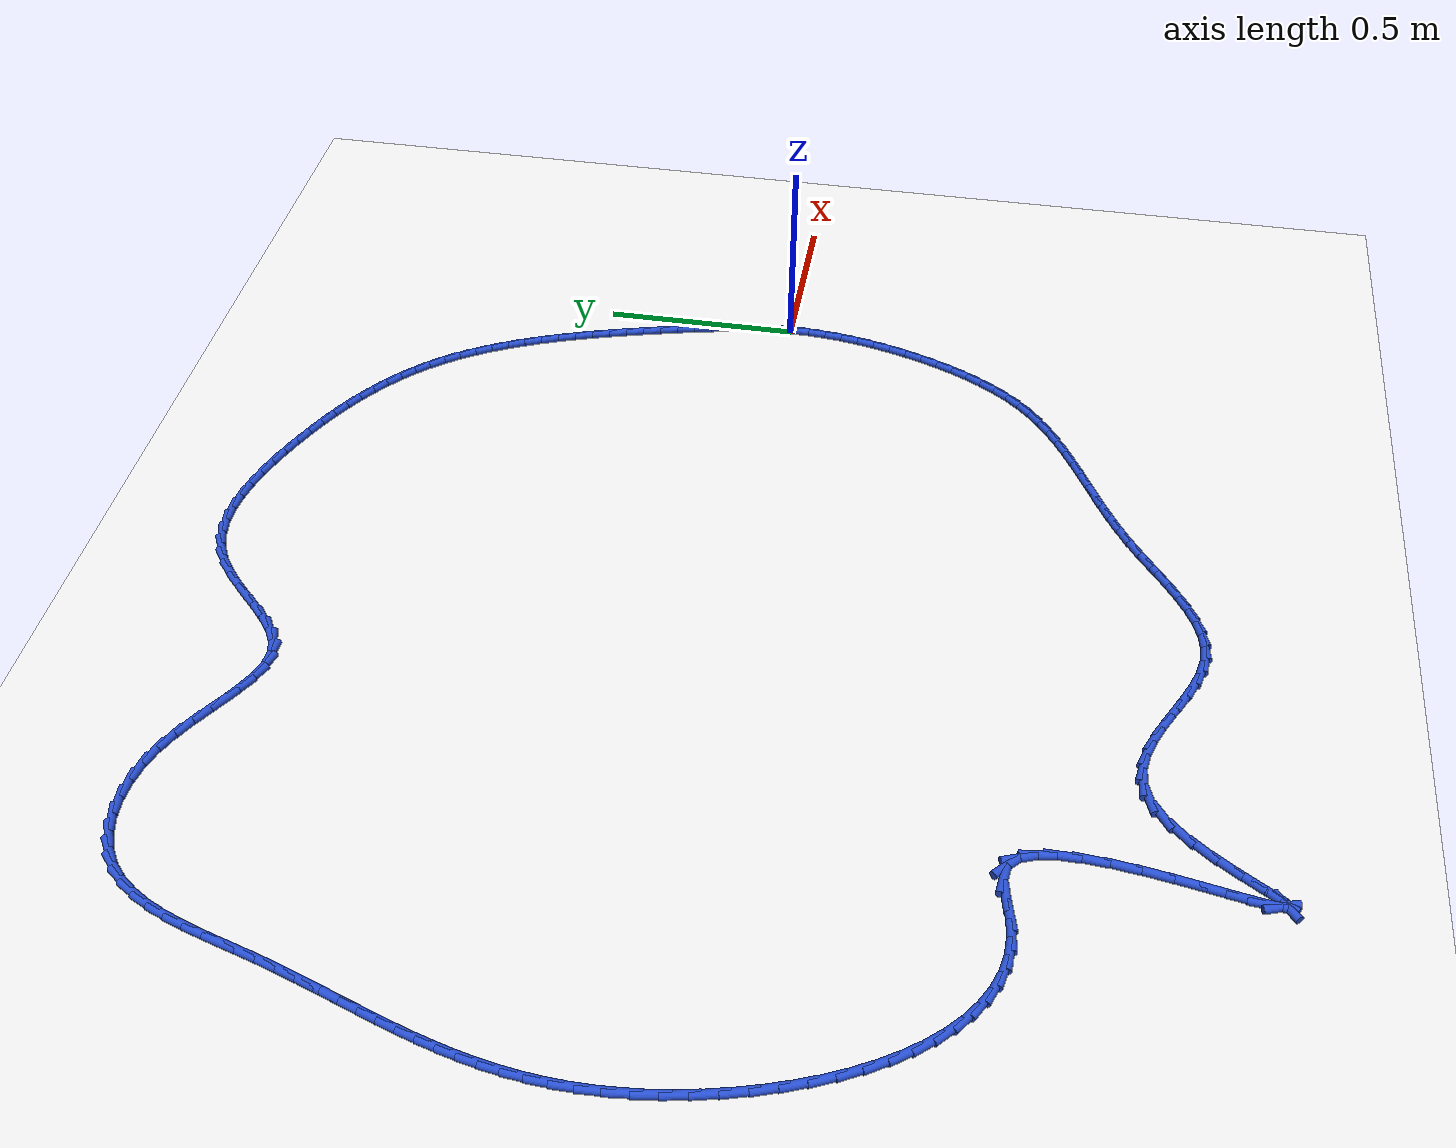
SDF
<sdf version="1.6">
 <world name="default">
  <light name="sun" type="directional">
   <pose>0 0 10 0 -0 0</pose>
   <diffuse>0.8 0.8 0.8 1</diffuse>
   <specular>0.2 0.2 0.2 1</specular>
   <attenuation>
    <range>1000</range>
    <constant>0.9</constant>
    <linear>0.01</linear>
    <quadratic>0.001</quadratic>
   </attenuation>
   <direction>-0.5 0.1 -0.9</direction>
  </light>
  <model name="ground_plane">
   <static>1</static>
   <link name="link">
    <collision name="collision">
     <geometry><plane><normal>0 0 1</normal><size>100 100</size></plane></geometry>
     <surface><friction><ode><mu>100</mu><mu2>50</mu2></ode></friction></surface>
    </collision>
    <visual name="visual">
     <cast_shadows>0</cast_shadows>
     <geometry><plane><normal>0 0 1</normal><size>100 100</size></plane></geometry>
     <material>
      <script><uri>file://media/materials/scripts/gazebo.material</uri><name>Gazebo/WhiteGlow</name></script>
     </material>
    </visual>
   </link>
  </model>
  <gravity>0 0 -9.8</gravity>
  <magnetic_field>6e-06 2.3e-05 -4.2e-05</magnetic_field>
  <atmosphere type="adiabatic"/>
  <physics name="default_physics" default="0" type="ode">
   <max_step_size>0.001</max_step_size>
   <real_time_factor>1</real_time_factor>
   <real_time_update_rate>1000</real_time_update_rate>
  </physics>
  <scene><ambient>0.4 0.4 0.4 1</ambient><background>0.7 0.7 0.7 1</background><shadows>1</shadows></scene>
  <spherical_coordinates>
   <surface_model>EARTH_WGS84</surface_model>
   <latitude_deg>0</latitude_deg>
   <longitude_deg>0</longitude_deg>
   <elevation>0</elevation>
   <heading_deg>0</heading_deg>
  </spherical_coordinates>
  <model name="line">
   <link name="link_0">
    <pose>-1.214306433183765e-17 -2.0816681711721685e-17 0.01 0 1.57 -1.5239779968371987</pose>
    <collision name="collision">
     <geometry><cylinder><radius>0.01</radius><length>0.08</length></cylinder></geometry>
    </collision>
    <visual name="visual">
     <material>
      <script><name>Gazebo/Blue</name><uri>file://media/materials/scripts/gazebo.material</uri></script>
     </material>
     <geometry><cylinder><radius>0.01</radius><length>0.08</length></cylinder></geometry>
    </visual>
   </link>
   <link name="link_1">
    <pose>-0.0021245154504253992 0.04534469606206822 0.01 0 1.57 -1.4723712508912976</pose>
    <collision name="collision">
     <geometry><cylinder><radius>0.01</radius><length>0.08</length></cylinder></geometry>
    </collision>
    <visual name="visual">
     <material>
      <script><name>Gazebo/Blue</name><uri>file://media/materials/scripts/gazebo.material</uri></script>
     </material>
     <geometry><cylinder><radius>0.01</radius><length>0.08</length></cylinder></geometry>
    </visual>
   </link>
   <link name="link_2">
    <pose>-0.006593316319034097 0.09060105988212223 0.01 0 1.57 -1.4277021264202554</pose>
    <collision name="collision">
     <geometry><cylinder><radius>0.01</radius><length>0.08</length></cylinder></geometry>
    </collision>
    <visual name="visual">
     <material>
      <script><name>Gazebo/Blue</name><uri>file://media/materials/scripts/gazebo.material</uri></script>
     </material>
     <geometry><cylinder><radius>0.01</radius><length>0.08</length></cylinder></geometry>
    </visual>
   </link>
   <link name="link_3">
    <pose>-0.013106867148751604 0.13580927209531798 0.01 0 1.57 -1.3900747745297217</pose>
    <collision name="collision">
     <geometry><cylinder><radius>0.01</radius><length>0.08</length></cylinder></geometry>
    </collision>
    <visual name="visual">
     <material>
      <script><name>Gazebo/Blue</name><uri>file://media/materials/scripts/gazebo.material</uri></script>
     </material>
     <geometry><cylinder><radius>0.01</radius><length>0.08</length></cylinder></geometry>
    </visual>
   </link>
   <link name="link_4">
    <pose>-0.021365632482503442 0.18100951333681153 0.01 0 1.57 -1.3594540855634945</pose>
    <collision name="collision">
     <geometry><cylinder><radius>0.01</radius><length>0.08</length></cylinder></geometry>
    </collision>
    <visual name="visual">
     <material>
      <script><name>Gazebo/Blue</name><uri>file://media/materials/scripts/gazebo.material</uri></script>
     </material>
     <geometry><cylinder><radius>0.01</radius><length>0.08</length></cylinder></geometry>
    </visual>
   </link>
   <link name="link_5">
    <pose>-0.031070076863215074 0.2262419642417586 0.01 0 1.57 -1.3357225294616695</pose>
    <collision name="collision">
     <geometry><cylinder><radius>0.01</radius><length>0.08</length></cylinder></geometry>
    </collision>
    <visual name="visual">
     <material>
      <script><name>Gazebo/Blue</name><uri>file://media/materials/scripts/gazebo.material</uri></script>
     </material>
     <geometry><cylinder><radius>0.01</radius><length>0.08</length></cylinder></geometry>
    </visual>
   </link>
   <link name="link_6">
    <pose>-0.04192066483381203 0.27154680544531534 0.01 0 1.57 -1.3187257069923661</pose>
    <collision name="collision">
     <geometry><cylinder><radius>0.01</radius><length>0.08</length></cylinder></geometry>
    </collision>
    <visual name="visual">
     <material>
      <script><name>Gazebo/Blue</name><uri>file://media/materials/scripts/gazebo.material</uri></script>
     </material>
     <geometry><cylinder><radius>0.01</radius><length>0.08</length></cylinder></geometry>
    </visual>
   </link>
   <link name="link_7">
    <pose>-0.05361786093721979 0.31696421758263754 0.01 0 1.57 -1.308159948260188</pose>
    <collision name="collision">
     <geometry><cylinder><radius>0.01</radius><length>0.08</length></cylinder></geometry>
    </collision>
    <visual name="visual">
     <material>
      <script><name>Gazebo/Blue</name><uri>file://media/materials/scripts/gazebo.material</uri></script>
     </material>
     <geometry><cylinder><radius>0.01</radius><length>0.08</length></cylinder></geometry>
    </visual>
   </link>
   <link name="link_8">
    <pose>-0.06586847644041166 0.3625315450831043 0.01 0 1.57 -1.2996111981379848</pose>
    <collision name="collision">
     <geometry><cylinder><radius>0.01</radius><length>0.08</length></cylinder></geometry>
    </collision>
    <visual name="visual">
     <material>
      <script><name>Gazebo/Blue</name><uri>file://media/materials/scripts/gazebo.material</uri></script>
     </material>
     <geometry><cylinder><radius>0.01</radius><length>0.08</length></cylinder></geometry>
    </visual>
   </link>
   <link name="link_9">
    <pose>-0.07856656411448149 0.408202458431606 0.01 0 1.57 -1.2881421093520649</pose>
    <collision name="collision">
     <geometry><cylinder><radius>0.01</radius><length>0.08</length></cylinder></geometry>
    </collision>
    <visual name="visual">
     <material>
      <script><name>Gazebo/Blue</name><uri>file://media/materials/scripts/gazebo.material</uri></script>
     </material>
     <geometry><cylinder><radius>0.01</radius><length>0.08</length></cylinder></geometry>
    </visual>
   </link>
   <link name="link_10">
    <pose>-0.09181969453499594 0.453835211891065 0.01 0 1.57 -1.2734338293448058</pose>
    <collision name="collision">
     <geometry><cylinder><radius>0.01</radius><length>0.08</length></cylinder></geometry>
    </collision>
    <visual name="visual">
     <material>
      <script><name>Gazebo/Blue</name><uri>file://media/materials/scripts/gazebo.material</uri></script>
     </material>
     <geometry><cylinder><radius>0.01</radius><length>0.08</length></cylinder></geometry>
    </visual>
   </link>
   <link name="link_11">
    <pose>-0.10574706868791374 0.4992828623600799 0.01 0 1.57 -1.2553971416705523</pose>
    <collision name="collision">
     <geometry><cylinder><radius>0.01</radius><length>0.08</length></cylinder></geometry>
    </collision>
    <visual name="visual">
     <material>
      <script><name>Gazebo/Blue</name><uri>file://media/materials/scripts/gazebo.material</uri></script>
     </material>
     <geometry><cylinder><radius>0.01</radius><length>0.08</length></cylinder></geometry>
    </visual>
   </link>
   <link name="link_12">
    <pose>-0.12046788755919356 0.5443984667372487 0.01 0 1.57 -1.2339089826335756</pose>
    <collision name="collision">
     <geometry><cylinder><radius>0.01</radius><length>0.08</length></cylinder></geometry>
    </collision>
    <visual name="visual">
     <material>
      <script><name>Gazebo/Blue</name><uri>file://media/materials/scripts/gazebo.material</uri></script>
     </material>
     <geometry><cylinder><radius>0.01</radius><length>0.08</length></cylinder></geometry>
    </visual>
   </link>
   <link name="link_13">
    <pose>-0.13610135213479416 0.5890350819211698 0.01 0 1.57 -1.2088162640019848</pose>
    <collision name="collision">
     <geometry><cylinder><radius>0.01</radius><length>0.08</length></cylinder></geometry>
    </collision>
    <visual name="visual">
     <material>
      <script><name>Gazebo/Blue</name><uri>file://media/materials/scripts/gazebo.material</uri></script>
     </material>
     <geometry><cylinder><radius>0.01</radius><length>0.08</length></cylinder></geometry>
    </visual>
   </link>
   <link name="link_14">
    <pose>-0.15276666340067419 0.6330457648104414 0.01 0 1.57 -1.1799410158548354</pose>
    <collision name="collision">
     <geometry><cylinder><radius>0.01</radius><length>0.08</length></cylinder></geometry>
    </collision>
    <visual name="visual">
     <material>
      <script><name>Gazebo/Blue</name><uri>file://media/materials/scripts/gazebo.material</uri></script>
     </material>
     <geometry><cylinder><radius>0.01</radius><length>0.08</length></cylinder></geometry>
    </visual>
   </link>
   <link name="link_15">
    <pose>-0.17058302234279238 0.6762835723036618 0.01 0 1.57 -1.1470876542077086</pose>
    <collision name="collision">
     <geometry><cylinder><radius>0.01</radius><length>0.08</length></cylinder></geometry>
    </collision>
    <visual name="visual">
     <material>
      <script><name>Gazebo/Blue</name><uri>file://media/materials/scripts/gazebo.material</uri></script>
     </material>
     <geometry><cylinder><radius>0.01</radius><length>0.08</length></cylinder></geometry>
    </visual>
   </link>
   <link name="link_16">
    <pose>-0.1896696299471074 0.7186015612994292 0.01 0 1.57 -1.1100533242488548</pose>
    <collision name="collision">
     <geometry><cylinder><radius>0.01</radius><length>0.08</length></cylinder></geometry>
    </collision>
    <visual name="visual">
     <material>
      <script><name>Gazebo/Blue</name><uri>file://media/materials/scripts/gazebo.material</uri></script>
     </material>
     <geometry><cylinder><radius>0.01</radius><length>0.08</length></cylinder></geometry>
    </visual>
   </link>
   <link name="link_17">
    <pose>-0.21014568719957794 0.7598527886963415 0.01 0 1.57 -1.0686423582017794</pose>
    <collision name="collision">
     <geometry><cylinder><radius>0.01</radius><length>0.08</length></cylinder></geometry>
    </collision>
    <visual name="visual">
     <material>
      <script><name>Gazebo/Blue</name><uri>file://media/materials/scripts/gazebo.material</uri></script>
     </material>
     <geometry><cylinder><radius>0.01</radius><length>0.08</length></cylinder></geometry>
    </visual>
   </link>
   <link name="link_18">
    <pose>-0.23213039508616282 0.7998903113929979 0.01 0 1.57 -1.0226858228537783</pose>
    <collision name="collision">
     <geometry><cylinder><radius>0.01</radius><length>0.08</length></cylinder></geometry>
    </collision>
    <visual name="visual">
     <material>
      <script><name>Gazebo/Blue</name><uri>file://media/materials/scripts/gazebo.material</uri></script>
     </material>
     <geometry><cylinder><radius>0.01</radius><length>0.08</length></cylinder></geometry>
    </visual>
   </link>
   <link name="link_19">
    <pose>-0.25574295459282054 0.838567186287996 0.01 0 1.57 -0.9720667740535098</pose>
    <collision name="collision">
     <geometry><cylinder><radius>0.01</radius><length>0.08</length></cylinder></geometry>
    </collision>
    <visual name="visual">
     <material>
      <script><name>Gazebo/Blue</name><uri>file://media/materials/scripts/gazebo.material</uri></script>
     </material>
     <geometry><cylinder><radius>0.01</radius><length>0.08</length></cylinder></geometry>
    </visual>
   </link>
   <link name="link_20">
    <pose>-0.28110256670551004 0.8757364702799344 0.01 0 1.57 -0.9167510090795917</pose>
    <collision name="collision">
     <geometry><cylinder><radius>0.01</radius><length>0.08</length></cylinder></geometry>
    </collision>
    <visual name="visual">
     <material>
      <script><name>Gazebo/Blue</name><uri>file://media/materials/scripts/gazebo.material</uri></script>
     </material>
     <geometry><cylinder><radius>0.01</radius><length>0.08</length></cylinder></geometry>
    </visual>
   </link>
   <link name="link_21">
    <pose>-0.30832843241019003 0.9112512202674112 0.01 0 1.57 -0.8568508711784869</pose>
    <collision name="collision">
     <geometry><cylinder><radius>0.01</radius><length>0.08</length></cylinder></geometry>
    </collision>
    <visual name="visual">
     <material>
      <script><name>Gazebo/Blue</name><uri>file://media/materials/scripts/gazebo.material</uri></script>
     </material>
     <geometry><cylinder><radius>0.01</radius><length>0.08</length></cylinder></geometry>
    </visual>
   </link>
   <link name="link_22">
    <pose>-0.3375388428029785 0.9449654326588343 0.01 0 1.57 -0.7950104594964325</pose>
    <collision name="collision">
     <geometry><cylinder><radius>0.01</radius><length>0.08</length></cylinder></geometry>
    </collision>
    <visual name="visual">
     <material>
      <script><name>Gazebo/Blue</name><uri>file://media/materials/scripts/gazebo.material</uri></script>
     </material>
     <geometry><cylinder><radius>0.01</radius><length>0.08</length></cylinder></geometry>
    </visual>
   </link>
   <link name="link_23">
    <pose>-0.3687773212004344 0.9768103055844293 0.01 0 1.57 -0.7357627584772974</pose>
    <collision name="collision">
     <geometry><cylinder><radius>0.01</radius><length>0.08</length></cylinder></geometry>
    </collision>
    <visual name="visual">
     <material>
      <script><name>Gazebo/Blue</name><uri>file://media/materials/scripts/gazebo.material</uri></script>
     </material>
     <geometry><cylinder><radius>0.01</radius><length>0.08</length></cylinder></geometry>
    </visual>
   </link>
   <link name="link_24">
    <pose>-0.40195811600002096 1.006850520426177 0.01 0 1.57 -0.6798365404967276</pose>
    <collision name="collision">
     <geometry><cylinder><radius>0.01</radius><length>0.08</length></cylinder></geometry>
    </collision>
    <visual name="visual">
     <material>
      <script><name>Gazebo/Blue</name><uri>file://media/materials/scripts/gazebo.material</uri></script>
     </material>
     <geometry><cylinder><radius>0.01</radius><length>0.08</length></cylinder></geometry>
    </visual>
   </link>
   <link name="link_25">
    <pose>-0.43698262886804506 1.035164023501446 0.01 0 1.57 -0.6274285808751373</pose>
    <collision name="collision">
     <geometry><cylinder><radius>0.01</radius><length>0.08</length></cylinder></geometry>
    </collision>
    <visual name="visual">
     <material>
      <script><name>Gazebo/Blue</name><uri>file://media/materials/scripts/gazebo.material</uri></script>
     </material>
     <geometry><cylinder><radius>0.01</radius><length>0.08</length></cylinder></geometry>
    </visual>
   </link>
   <link name="link_26">
    <pose>-0.4737522614708131 1.0618287611276054 0.01 0 1.57 -0.578630373063824</pose>
    <collision name="collision">
     <geometry><cylinder><radius>0.01</radius><length>0.08</length></cylinder></geometry>
    </collision>
    <visual name="visual">
     <material>
      <script><name>Gazebo/Blue</name><uri>file://media/materials/scripts/gazebo.material</uri></script>
     </material>
     <geometry><cylinder><radius>0.01</radius><length>0.08</length></cylinder></geometry>
    </visual>
   </link>
   <link name="link_27">
    <pose>-0.5121684154746318 1.0869226796220237 0.01 0 1.57 -0.5334468165381331</pose>
    <collision name="collision">
     <geometry><cylinder><radius>0.01</radius><length>0.08</length></cylinder></geometry>
    </collision>
    <visual name="visual">
     <material>
      <script><name>Gazebo/Blue</name><uri>file://media/materials/scripts/gazebo.material</uri></script>
     </material>
     <geometry><cylinder><radius>0.01</radius><length>0.08</length></cylinder></geometry>
    </visual>
   </link>
   <link name="link_28">
    <pose>-0.5521324925458079 1.11052372530207 0.01 0 1.57 -0.4918160845121168</pose>
    <collision name="collision">
     <geometry><cylinder><radius>0.01</radius><length>0.08</length></cylinder></geometry>
    </collision>
    <visual name="visual">
     <material>
      <script><name>Gazebo/Blue</name><uri>file://media/materials/scripts/gazebo.material</uri></script>
     </material>
     <geometry><cylinder><radius>0.01</radius><length>0.08</length></cylinder></geometry>
    </visual>
   </link>
   <link name="link_29">
    <pose>-0.5935458943506481 1.1327098444851142 0.01 0 1.57 -0.45362842655288443</pose>
    <collision name="collision">
     <geometry><cylinder><radius>0.01</radius><length>0.08</length></cylinder></geometry>
    </collision>
    <visual name="visual">
     <material>
      <script><name>Gazebo/Blue</name><uri>file://media/materials/scripts/gazebo.material</uri></script>
     </material>
     <geometry><cylinder><radius>0.01</radius><length>0.08</length></cylinder></geometry>
    </visual>
   </link>
   <link name="link_30">
    <pose>-0.636310022555459 1.153558983488524 0.01 0 1.57 -0.41874259654983365</pose>
    <collision name="collision">
     <geometry><cylinder><radius>0.01</radius><length>0.08</length></cylinder></geometry>
    </collision>
    <visual name="visual">
     <material>
      <script><name>Gazebo/Blue</name><uri>file://media/materials/scripts/gazebo.material</uri></script>
     </material>
     <geometry><cylinder><radius>0.01</radius><length>0.08</length></cylinder></geometry>
    </visual>
   </link>
   <link name="link_31">
    <pose>-0.680326278826547 1.1731490886296692 0.01 0 1.57 -0.3869993596042835</pose>
    <collision name="collision">
     <geometry><cylinder><radius>0.01</radius><length>0.08</length></cylinder></geometry>
    </collision>
    <visual name="visual">
     <material>
      <script><name>Gazebo/Blue</name><uri>file://media/materials/scripts/gazebo.material</uri></script>
     </material>
     <geometry><cylinder><radius>0.01</radius><length>0.08</length></cylinder></geometry>
    </visual>
   </link>
   <link name="link_32">
    <pose>-0.7254960648302193 1.1915581062259184 0.01 0 1.57 -0.3579851384546086</pose>
    <collision name="collision">
     <geometry><cylinder><radius>0.01</radius><length>0.08</length></cylinder></geometry>
    </collision>
    <visual name="visual">
     <material>
      <script><name>Gazebo/Blue</name><uri>file://media/materials/scripts/gazebo.material</uri></script>
     </material>
     <geometry><cylinder><radius>0.01</radius><length>0.08</length></cylinder></geometry>
    </visual>
   </link>
   <link name="link_33">
    <pose>-0.7717162378962404 1.2088492701658993 0.01 0 1.57 -0.3251932840505033</pose>
    <collision name="collision">
     <geometry><cylinder><radius>0.01</radius><length>0.08</length></cylinder></geometry>
    </collision>
    <visual name="visual">
     <material>
      <script><name>Gazebo/Blue</name><uri>file://media/materials/scripts/gazebo.material</uri></script>
     </material>
     <geometry><cylinder><radius>0.01</radius><length>0.08</length></cylinder></geometry>
    </visual>
   </link>
   <link name="link_34">
    <pose>-0.8187686919033086 1.2247136166442205 0.01 0 1.57 -0.2812549926991139</pose>
    <collision name="collision">
     <geometry><cylinder><radius>0.01</radius><length>0.08</length></cylinder></geometry>
    </collision>
    <visual name="visual">
     <material>
      <script><name>Gazebo/Blue</name><uri>file://media/materials/scripts/gazebo.material</uri></script>
     </material>
     <geometry><cylinder><radius>0.01</radius><length>0.08</length></cylinder></geometry>
    </visual>
   </link>
   <link name="link_35">
    <pose>-0.8663142372746581 1.238450170459786 0.01 0 1.57 -0.2244659714510763</pose>
    <collision name="collision">
     <geometry><cylinder><radius>0.01</radius><length>0.08</length></cylinder></geometry>
    </collision>
    <visual name="visual">
     <material>
      <script><name>Gazebo/Blue</name><uri>file://media/materials/scripts/gazebo.material</uri></script>
     </material>
     <geometry><cylinder><radius>0.01</radius><length>0.08</length></cylinder></geometry>
    </visual>
   </link>
   <link name="link_36">
    <pose>-0.9140079150638308 1.2493392779004138 0.01 0 1.57 -0.15295369816399138</pose>
    <collision name="collision">
     <geometry><cylinder><radius>0.01</radius><length>0.08</length></cylinder></geometry>
    </collision>
    <visual name="visual">
     <material>
      <script><name>Gazebo/Blue</name><uri>file://media/materials/scripts/gazebo.material</uri></script>
     </material>
     <geometry><cylinder><radius>0.01</radius><length>0.08</length></cylinder></geometry>
    </visual>
   </link>
   <link name="link_37">
    <pose>-0.9615047663243695 1.2566612852539232 0.01 0 1.57 -0.06455185236638566</pose>
    <collision name="collision">
     <geometry><cylinder><radius>0.01</radius><length>0.08</length></cylinder></geometry>
    </collision>
    <visual name="visual">
     <material>
      <script><name>Gazebo/Blue</name><uri>file://media/materials/scripts/gazebo.material</uri></script>
     </material>
     <geometry><cylinder><radius>0.01</radius><length>0.08</length></cylinder></geometry>
    </visual>
   </link>
   <link name="link_38">
    <pose>-1.0084598321098155 1.259696538808132 0.01 0 1.57 0.04276153985517493</pose>
    <collision name="collision">
     <geometry><cylinder><radius>0.01</radius><length>0.08</length></cylinder></geometry>
    </collision>
    <visual name="visual">
     <material>
      <script><name>Gazebo/Blue</name><uri>file://media/materials/scripts/gazebo.material</uri></script>
     </material>
     <geometry><cylinder><radius>0.01</radius><length>0.08</length></cylinder></geometry>
    </visual>
   </link>
   <link name="link_39">
    <pose>-1.0545281534737119 1.257725384850859 0.01 0 1.57 0.1700152480711578</pose>
    <collision name="collision">
     <geometry><cylinder><radius>0.01</radius><length>0.08</length></cylinder></geometry>
    </collision>
    <visual name="visual">
     <material>
      <script><name>Gazebo/Blue</name><uri>file://media/materials/scripts/gazebo.material</uri></script>
     </material>
     <geometry><cylinder><radius>0.01</radius><length>0.08</length></cylinder></geometry>
    </visual>
   </link>
   <link name="link_40">
    <pose>-1.0993647714696009 1.2500281696699225 0.01 0 1.57 0.3159755409349067</pose>
    <collision name="collision">
     <geometry><cylinder><radius>0.01</radius><length>0.08</length></cylinder></geometry>
    </collision>
    <visual name="visual">
     <material>
      <script><name>Gazebo/Blue</name><uri>file://media/materials/scripts/gazebo.material</uri></script>
     </material>
     <geometry><cylinder><radius>0.01</radius><length>0.08</length></cylinder></geometry>
    </visual>
   </link>
   <link name="link_41">
    <pose>-1.1426247271510244 1.2358852395531414 0.01 0 1.57 0.47585016034493594</pose>
    <collision name="collision">
     <geometry><cylinder><radius>0.01</radius><length>0.08</length></cylinder></geometry>
    </collision>
    <visual name="visual">
     <material>
      <script><name>Gazebo/Blue</name><uri>file://media/materials/scripts/gazebo.material</uri></script>
     </material>
     <geometry><cylinder><radius>0.01</radius><length>0.08</length></cylinder></geometry>
    </visual>
   </link>
   <link name="link_42">
    <pose>-1.183964063220118 1.2145811123032588 0.01 0 1.57 0.6237546364896369</pose>
    <collision name="collision">
     <geometry><cylinder><radius>0.01</radius><length>0.08</length></cylinder></geometry>
    </collision>
    <visual name="visual">
     <material>
      <script><name>Gazebo/Blue</name><uri>file://media/materials/scripts/gazebo.material</uri></script>
     </material>
     <geometry><cylinder><radius>0.01</radius><length>0.08</length></cylinder></geometry>
    </visual>
   </link>
   <link name="link_43">
    <pose>-1.2232564410881226 1.1863066112871292 0.01 0 1.57 0.7205555855280511</pose>
    <collision name="collision">
     <geometry><cylinder><radius>0.01</radius><length>0.08</length></cylinder></geometry>
    </collision>
    <visual name="visual">
     <material>
      <script><name>Gazebo/Blue</name><uri>file://media/materials/scripts/gazebo.material</uri></script>
     </material>
     <geometry><cylinder><radius>0.01</radius><length>0.08</length></cylinder></geometry>
    </visual>
   </link>
   <link name="link_44">
    <pose>-1.26086367177241 1.1532855316963693 0.01 0 1.57 0.7702737062106125</pose>
    <collision name="collision">
     <geometry><cylinder><radius>0.01</radius><length>0.08</length></cylinder></geometry>
    </collision>
    <visual name="visual">
     <material>
      <script><name>Gazebo/Blue</name><uri>file://media/materials/scripts/gazebo.material</uri></script>
     </material>
     <geometry><cylinder><radius>0.01</radius><length>0.08</length></cylinder></geometry>
    </visual>
   </link>
   <link name="link_45">
    <pose>-1.2972140230871396 1.1180184379624714 0.01 0 1.57 0.7781791566224082</pose>
    <collision name="collision">
     <geometry><cylinder><radius>0.01</radius><length>0.08</length></cylinder></geometry>
    </collision>
    <visual name="visual">
     <material>
      <script><name>Gazebo/Blue</name><uri>file://media/materials/scripts/gazebo.material</uri></script>
     </material>
     <geometry><cylinder><radius>0.01</radius><length>0.08</length></cylinder></geometry>
    </visual>
   </link>
   <link name="link_46">
    <pose>-1.3327357628464715 1.0830058945169276 0.01 0 1.57 0.7429182836827948</pose>
    <collision name="collision">
     <geometry><cylinder><radius>0.01</radius><length>0.08</length></cylinder></geometry>
    </collision>
    <visual name="visual">
     <material>
      <script><name>Gazebo/Blue</name><uri>file://media/materials/scripts/gazebo.material</uri></script>
     </material>
     <geometry><cylinder><radius>0.01</radius><length>0.08</length></cylinder></geometry>
    </visual>
   </link>
   <link name="link_47">
    <pose>-1.3678571588645654 1.0507484657912325 0.01 0 1.57 0.6550484692493531</pose>
    <collision name="collision">
     <geometry><cylinder><radius>0.01</radius><length>0.08</length></cylinder></geometry>
    </collision>
    <visual name="visual">
     <material>
      <script><name>Gazebo/Blue</name><uri>file://media/materials/scripts/gazebo.material</uri></script>
     </material>
     <geometry><cylinder><radius>0.01</radius><length>0.08</length></cylinder></geometry>
    </visual>
   </link>
   <link name="link_48">
    <pose>-1.4030064789555803 1.0237467162168776 0.01 0 1.57 0.49553609593984116</pose>
    <collision name="collision">
     <geometry><cylinder><radius>0.01</radius><length>0.08</length></cylinder></geometry>
    </collision>
    <visual name="visual">
     <material>
      <script><name>Gazebo/Blue</name><uri>file://media/materials/scripts/gazebo.material</uri></script>
     </material>
     <geometry><cylinder><radius>0.01</radius><length>0.08</length></cylinder></geometry>
    </visual>
   </link>
   <link name="link_49">
    <pose>-1.4386119909336765 1.0045012102253554 0.01 0 1.57 0.24184631108589383</pose>
    <collision name="collision">
     <geometry><cylinder><radius>0.01</radius><length>0.08</length></cylinder></geometry>
    </collision>
    <visual name="visual">
     <material>
      <script><name>Gazebo/Blue</name><uri>file://media/materials/scripts/gazebo.material</uri></script>
     </material>
     <geometry><cylinder><radius>0.01</radius><length>0.08</length></cylinder></geometry>
    </visual>
   </link>
   <link name="link_50">
    <pose>-1.4751009922724188 0.995500305186169 0.01 0 1.57 -0.05921750002147579</pose>
    <collision name="collision">
     <geometry><cylinder><radius>0.01</radius><length>0.08</length></cylinder></geometry>
    </collision>
    <visual name="visual">
     <material>
      <script><name>Gazebo/Blue</name><uri>file://media/materials/scripts/gazebo.material</uri></script>
     </material>
     <geometry><cylinder><radius>0.01</radius><length>0.08</length></cylinder></geometry>
    </visual>
   </link>
   <link name="link_51">
    <pose>-1.5127816975797825 0.9977342742598079 0.01 0 1.57 -0.28800717033451306</pose>
    <collision name="collision">
     <geometry><cylinder><radius>0.01</radius><length>0.08</length></cylinder></geometry>
    </collision>
    <visual name="visual">
     <material>
      <script><name>Gazebo/Blue</name><uri>file://media/materials/scripts/gazebo.material</uri></script>
     </material>
     <geometry><cylinder><radius>0.01</radius><length>0.08</length></cylinder></geometry>
    </visual>
   </link>
   <link name="link_52">
    <pose>-1.5517301402263604 1.0092725082142406 0.01 0 1.57 -0.4322167276771261</pose>
    <collision name="collision">
     <geometry><cylinder><radius>0.01</radius><length>0.08</length></cylinder></geometry>
    </collision>
    <visual name="visual">
     <material>
      <script><name>Gazebo/Blue</name><uri>file://media/materials/scripts/gazebo.material</uri></script>
     </material>
     <geometry><cylinder><radius>0.01</radius><length>0.08</length></cylinder></geometry>
    </visual>
   </link>
   <link name="link_53">
    <pose>-1.5919955507576256 1.0278472133797936 0.01 0 1.57 -0.5110309099938437</pose>
    <collision name="collision">
     <geometry><cylinder><radius>0.01</radius><length>0.08</length></cylinder></geometry>
    </collision>
    <visual name="visual">
     <material>
      <script><name>Gazebo/Blue</name><uri>file://media/materials/scripts/gazebo.material</uri></script>
     </material>
     <geometry><cylinder><radius>0.01</radius><length>0.08</length></cylinder></geometry>
    </visual>
   </link>
   <link name="link_54">
    <pose>-1.633627159719053 1.051190596086793 0.01 0 1.57 -0.5406935024960966</pose>
    <collision name="collision">
     <geometry><cylinder><radius>0.01</radius><length>0.08</length></cylinder></geometry>
    </collision>
    <visual name="visual">
     <material>
      <script><name>Gazebo/Blue</name><uri>file://media/materials/scripts/gazebo.material</uri></script>
     </material>
     <geometry><cylinder><radius>0.01</radius><length>0.08</length></cylinder></geometry>
    </visual>
   </link>
   <link name="link_55">
    <pose>-1.6766741976561166 1.0770348626655648 0.01 0 1.57 -0.5299531028772743</pose>
    <collision name="collision">
     <geometry><cylinder><radius>0.01</radius><length>0.08</length></cylinder></geometry>
    </collision>
    <visual name="visual">
     <material>
      <script><name>Gazebo/Blue</name><uri>file://media/materials/scripts/gazebo.material</uri></script>
     </material>
     <geometry><cylinder><radius>0.01</radius><length>0.08</length></cylinder></geometry>
    </visual>
   </link>
   <link name="link_56">
    <pose>-1.7211858951142895 1.103112219446435 0.01 0 1.57 -0.48138759618964533</pose>
    <collision name="collision">
     <geometry><cylinder><radius>0.01</radius><length>0.08</length></cylinder></geometry>
    </collision>
    <visual name="visual">
     <material>
      <script><name>Gazebo/Blue</name><uri>file://media/materials/scripts/gazebo.material</uri></script>
     </material>
     <geometry><cylinder><radius>0.01</radius><length>0.08</length></cylinder></geometry>
    </visual>
   </link>
   <link name="link_57">
    <pose>-1.7672114826390464 1.1271548727597296 0.01 0 1.57 -0.39321096665533933</pose>
    <collision name="collision">
     <geometry><cylinder><radius>0.01</radius><length>0.08</length></cylinder></geometry>
    </collision>
    <visual name="visual">
     <material>
      <script><name>Gazebo/Blue</name><uri>file://media/materials/scripts/gazebo.material</uri></script>
     </material>
     <geometry><cylinder><radius>0.01</radius><length>0.08</length></cylinder></geometry>
    </visual>
   </link>
   <link name="link_58">
    <pose>-1.8148000801979667 1.1468952607210072 0.01 0 1.57 -0.27202221343145705</pose>
    <collision name="collision">
     <geometry><cylinder><radius>0.01</radius><length>0.08</length></cylinder></geometry>
    </collision>
    <visual name="visual">
     <material>
      <script><name>Gazebo/Blue</name><uri>file://media/materials/scripts/gazebo.material</uri></script>
     </material>
     <geometry><cylinder><radius>0.01</radius><length>0.08</length></cylinder></geometry>
    </visual>
   </link>
   <link name="link_59">
    <pose>-1.8637678386730474 1.160554154070002 0.01 0 1.57 -0.14692527199367256</pose>
    <collision name="collision">
     <geometry><cylinder><radius>0.01</radius><length>0.08</length></cylinder></geometry>
    </collision>
    <visual name="visual">
     <material>
      <script><name>Gazebo/Blue</name><uri>file://media/materials/scripts/gazebo.material</uri></script>
     </material>
     <geometry><cylinder><radius>0.01</radius><length>0.08</length></cylinder></geometry>
    </visual>
   </link>
   <link name="link_60">
    <pose>-1.9132065490873316 1.1678706732875328 0.01 0 1.57 -0.0206168953785066</pose>
    <collision name="collision">
     <geometry><cylinder><radius>0.01</radius><length>0.08</length></cylinder></geometry>
    </collision>
    <visual name="visual">
     <material>
      <script><name>Gazebo/Blue</name><uri>file://media/materials/scripts/gazebo.material</uri></script>
     </material>
     <geometry><cylinder><radius>0.01</radius><length>0.08</length></cylinder></geometry>
    </visual>
   </link>
   <link name="link_61">
    <pose>-1.9620676287867778 1.1688781798088457 0.01 0 1.57 0.1110718210881586</pose>
    <collision name="collision">
     <geometry><cylinder><radius>0.01</radius><length>0.08</length></cylinder></geometry>
    </collision>
    <visual name="visual">
     <material>
      <script><name>Gazebo/Blue</name><uri>file://media/materials/scripts/gazebo.material</uri></script>
     </material>
     <geometry><cylinder><radius>0.01</radius><length>0.08</length></cylinder></geometry>
    </visual>
   </link>
   <link name="link_62">
    <pose>-2.0093024951173493 1.1636100350691867 0.01 0 1.57 0.2527870017412311</pose>
    <collision name="collision">
     <geometry><cylinder><radius>0.01</radius><length>0.08</length></cylinder></geometry>
    </collision>
    <visual name="visual">
     <material>
      <script><name>Gazebo/Blue</name><uri>file://media/materials/scripts/gazebo.material</uri></script>
     </material>
     <geometry><cylinder><radius>0.01</radius><length>0.08</length></cylinder></geometry>
    </visual>
   </link>
   <link name="link_63">
    <pose>-2.053862565425007 1.1520996005038016 0.01 0 1.57 0.40939145685200207</pose>
    <collision name="collision">
     <geometry><cylinder><radius>0.01</radius><length>0.08</length></cylinder></geometry>
    </collision>
    <visual name="visual">
     <material>
      <script><name>Gazebo/Blue</name><uri>file://media/materials/scripts/gazebo.material</uri></script>
     </material>
     <geometry><cylinder><radius>0.01</radius><length>0.08</length></cylinder></geometry>
    </visual>
   </link>
   <link name="link_64">
    <pose>-2.0946992570557117 1.1343802375479368 0.01 0 1.57 0.5846783201029622</pose>
    <collision name="collision">
     <geometry><cylinder><radius>0.01</radius><length>0.08</length></cylinder></geometry>
    </collision>
    <visual name="visual">
     <material>
      <script><name>Gazebo/Blue</name><uri>file://media/materials/scripts/gazebo.material</uri></script>
     </material>
     <geometry><cylinder><radius>0.01</radius><length>0.08</length></cylinder></geometry>
    </visual>
   </link>
   <link name="link_65">
    <pose>-2.1307860236112193 1.1104952900122271 0.01 0 1.57 0.7627107232614537</pose>
    <collision name="collision">
     <geometry><cylinder><radius>0.01</radius><length>0.08</length></cylinder></geometry>
    </collision>
    <visual name="visual">
     <material>
      <script><name>Gazebo/Blue</name><uri>file://media/materials/scripts/gazebo.material</uri></script>
     </material>
     <geometry><cylinder><radius>0.01</radius><length>0.08</length></cylinder></geometry>
    </visual>
   </link>
   <link name="link_66">
    <pose>-2.161836002167271 1.0808231766935328 0.01 0 1.57 0.9159666856900901</pose>
    <collision name="collision">
     <geometry><cylinder><radius>0.01</radius><length>0.08</length></cylinder></geometry>
    </collision>
    <visual name="visual">
     <material>
      <script><name>Gazebo/Blue</name><uri>file://media/materials/scripts/gazebo.material</uri></script>
     </material>
     <geometry><cylinder><radius>0.01</radius><length>0.08</length></cylinder></geometry>
    </visual>
   </link>
   <link name="link_67">
    <pose>-2.188460529802021 1.0461491990135392 0.01 0 1.57 1.0390309750069187</pose>
    <collision name="collision">
     <geometry><cylinder><radius>0.01</radius><length>0.08</length></cylinder></geometry>
    </collision>
    <visual name="visual">
     <material>
      <script><name>Gazebo/Blue</name><uri>file://media/materials/scripts/gazebo.material</uri></script>
     </material>
     <geometry><cylinder><radius>0.01</radius><length>0.08</length></cylinder></geometry>
    </visual>
   </link>
   <link name="link_68">
    <pose>-2.211325058319956 1.0072831722458935 0.01 0 1.57 1.1331176461598893</pose>
    <collision name="collision">
     <geometry><cylinder><radius>0.01</radius><length>0.08</length></cylinder></geometry>
    </collision>
    <visual name="visual">
     <material>
      <script><name>Gazebo/Blue</name><uri>file://media/materials/scripts/gazebo.material</uri></script>
     </material>
     <geometry><cylinder><radius>0.01</radius><length>0.08</length></cylinder></geometry>
    </visual>
   </link>
   <link name="link_69">
    <pose>-2.2310950395255578 0.9650349116642417 0.01 0 1.57 1.2016383731990814</pose>
    <collision name="collision">
     <geometry><cylinder><radius>0.01</radius><length>0.08</length></cylinder></geometry>
    </collision>
    <visual name="visual">
     <material>
      <script><name>Gazebo/Blue</name><uri>file://media/materials/scripts/gazebo.material</uri></script>
     </material>
     <geometry><cylinder><radius>0.01</radius><length>0.08</length></cylinder></geometry>
    </visual>
   </link>
   <link name="link_70">
    <pose>-2.2484359252233133 0.9202142325422318 0.01 0 1.57 1.2480900888142372</pose>
    <collision name="collision">
     <geometry><cylinder><radius>0.01</radius><length>0.08</length></cylinder></geometry>
    </collision>
    <visual name="visual">
     <material>
      <script><name>Gazebo/Blue</name><uri>file://media/materials/scripts/gazebo.material</uri></script>
     </material>
     <geometry><cylinder><radius>0.01</radius><length>0.08</length></cylinder></geometry>
    </visual>
   </link>
   <link name="link_71">
    <pose>-2.264013167217706 0.8736309501535097 0.01 0 1.57 1.2751331214356962</pose>
    <collision name="collision">
     <geometry><cylinder><radius>0.01</radius><length>0.08</length></cylinder></geometry>
    </collision>
    <visual name="visual">
     <material>
      <script><name>Gazebo/Blue</name><uri>file://media/materials/scripts/gazebo.material</uri></script>
     </material>
     <geometry><cylinder><radius>0.01</radius><length>0.08</length></cylinder></geometry>
    </visual>
   </link>
   <link name="link_72">
    <pose>-2.278492217313222 0.8260948797717232 0.01 0 1.57 1.284299760770772</pose>
    <collision name="collision">
     <geometry><cylinder><radius>0.01</radius><length>0.08</length></cylinder></geometry>
    </collision>
    <visual name="visual">
     <material>
      <script><name>Gazebo/Blue</name><uri>file://media/materials/scripts/gazebo.material</uri></script>
     </material>
     <geometry><cylinder><radius>0.01</radius><length>0.08</length></cylinder></geometry>
    </visual>
   </link>
   <link name="link_73">
    <pose>-2.292538527314345 0.7784158366705188 0.01 0 1.57 1.2759958923981525</pose>
    <collision name="collision">
     <geometry><cylinder><radius>0.01</radius><length>0.08</length></cylinder></geometry>
    </collision>
    <visual name="visual">
     <material>
      <script><name>Gazebo/Blue</name><uri>file://media/materials/scripts/gazebo.material</uri></script>
     </material>
     <geometry><cylinder><radius>0.01</radius><length>0.08</length></cylinder></geometry>
    </visual>
   </link>
   <link name="link_74">
    <pose>-2.306814683928416 0.7314003934572242 0.01 0 1.57 1.2571057335215645</pose>
    <collision name="collision">
     <geometry><cylinder><radius>0.01</radius><length>0.08</length></cylinder></geometry>
    </collision>
    <visual name="visual">
     <material>
      <script><name>Gazebo/Blue</name><uri>file://media/materials/scripts/gazebo.material</uri></script>
     </material>
     <geometry><cylinder><radius>0.01</radius><length>0.08</length></cylinder></geometry>
    </visual>
   </link>
   <link name="link_75">
    <pose>-2.321695354054454 0.6855292601879672 0.01 0 1.57 1.2414173218205748</pose>
    <collision name="collision">
     <geometry><cylinder><radius>0.01</radius><length>0.08</length></cylinder></geometry>
    </collision>
    <visual name="visual">
     <material>
      <script><name>Gazebo/Blue</name><uri>file://media/materials/scripts/gazebo.material</uri></script>
     </material>
     <geometry><cylinder><radius>0.01</radius><length>0.08</length></cylinder></geometry>
    </visual>
   </link>
   <link name="link_76">
    <pose>-2.337025129170106 0.6406832169239687 0.01 0 1.57 1.2307891896166439</pose>
    <collision name="collision">
     <geometry><cylinder><radius>0.01</radius><length>0.08</length></cylinder></geometry>
    </collision>
    <visual name="visual">
     <material>
      <script><name>Gazebo/Blue</name><uri>file://media/materials/scripts/gazebo.material</uri></script>
     </material>
     <geometry><cylinder><radius>0.01</radius><length>0.08</length></cylinder></geometry>
    </visual>
   </link>
   <link name="link_77">
    <pose>-2.352591573334029 0.5966785011013751 0.01 0 1.57 1.2255327627346562</pose>
    <collision name="collision">
     <geometry><cylinder><radius>0.01</radius><length>0.08</length></cylinder></geometry>
    </collision>
    <visual name="visual">
     <material>
      <script><name>Gazebo/Blue</name><uri>file://media/materials/scripts/gazebo.material</uri></script>
     </material>
     <geometry><cylinder><radius>0.01</radius><length>0.08</length></cylinder></geometry>
    </visual>
   </link>
   <link name="link_78">
    <pose>-2.3681822506048786 0.5533313501563347 0.01 0 1.57 1.2259002304611057</pose>
    <collision name="collision">
     <geometry><cylinder><radius>0.01</radius><length>0.08</length></cylinder></geometry>
    </collision>
    <visual name="visual">
     <material>
      <script><name>Gazebo/Blue</name><uri>file://media/materials/scripts/gazebo.material</uri></script>
     </material>
     <geometry><cylinder><radius>0.01</radius><length>0.08</length></cylinder></geometry>
    </visual>
   </link>
   <link name="link_79">
    <pose>-2.3835847250413167 0.5104580015249949 0.01 0 1.57 1.2320794972122886</pose>
    <collision name="collision">
     <geometry><cylinder><radius>0.01</radius><length>0.08</length></cylinder></geometry>
    </collision>
    <visual name="visual">
     <material>
      <script><name>Gazebo/Blue</name><uri>file://media/materials/scripts/gazebo.material</uri></script>
     </material>
     <geometry><cylinder><radius>0.01</radius><length>0.08</length></cylinder></geometry>
    </visual>
   </link>
   <link name="link_80">
    <pose>-2.3985865607019967 0.46787469264350184 0.01 0 1.57 1.2441857638782754</pose>
    <collision name="collision">
     <geometry><cylinder><radius>0.01</radius><length>0.08</length></cylinder></geometry>
    </collision>
    <visual name="visual">
     <material>
      <script><name>Gazebo/Blue</name><uri>file://media/materials/scripts/gazebo.material</uri></script>
     </material>
     <geometry><cylinder><radius>0.01</radius><length>0.08</length></cylinder></geometry>
    </visual>
   </link>
   <link name="link_81">
    <pose>-2.4129753216455785 0.4253976609480045 0.01 0 1.57 1.2622490584406183</pose>
    <collision name="collision">
     <geometry><cylinder><radius>0.01</radius><length>0.08</length></cylinder></geometry>
    </collision>
    <visual name="visual">
     <material>
      <script><name>Gazebo/Blue</name><uri>file://media/materials/scripts/gazebo.material</uri></script>
     </material>
     <geometry><cylinder><radius>0.01</radius><length>0.08</length></cylinder></geometry>
    </visual>
   </link>
   <link name="link_82">
    <pose>-2.426538571930719 0.38284314387464957 0.01 0 1.57 1.2861979775170518</pose>
    <collision name="collision">
     <geometry><cylinder><radius>0.01</radius><length>0.08</length></cylinder></geometry>
    </collision>
    <visual name="visual">
     <material>
      <script><name>Gazebo/Blue</name><uri>file://media/materials/scripts/gazebo.material</uri></script>
     </material>
     <geometry><cylinder><radius>0.01</radius><length>0.08</length></cylinder></geometry>
    </visual>
   </link>
   <link name="link_83">
    <pose>-2.4390638756160756 0.3400273788595839 0.01 0 1.57 1.315841167530883</pose>
    <collision name="collision">
     <geometry><cylinder><radius>0.01</radius><length>0.08</length></cylinder></geometry>
    </collision>
    <visual name="visual">
     <material>
      <script><name>Gazebo/Blue</name><uri>file://media/materials/scripts/gazebo.material</uri></script>
     </material>
     <geometry><cylinder><radius>0.01</radius><length>0.08</length></cylinder></geometry>
    </visual>
   </link>
   <link name="link_84">
    <pose>-2.450338796760307 0.29676660333895605 0.01 0 1.57 1.3508495517596677</pose>
    <collision name="collision">
     <geometry><cylinder><radius>0.01</radius><length>0.08</length></cylinder></geometry>
    </collision>
    <visual name="visual">
     <material>
      <script><name>Gazebo/Blue</name><uri>file://media/materials/scripts/gazebo.material</uri></script>
     </material>
     <geometry><cylinder><radius>0.01</radius><length>0.08</length></cylinder></geometry>
    </visual>
   </link>
   <link name="link_85">
    <pose>-2.46015089942207 0.25287705474891226 0.01 0 1.57 1.3907436875496384</pose>
    <collision name="collision">
     <geometry><cylinder><radius>0.01</radius><length>0.08</length></cylinder></geometry>
    </collision>
    <visual name="visual">
     <material>
      <script><name>Gazebo/Blue</name><uri>file://media/materials/scripts/gazebo.material</uri></script>
     </material>
     <geometry><cylinder><radius>0.01</radius><length>0.08</length></cylinder></geometry>
    </visual>
   </link>
   <link name="link_86">
    <pose>-2.4682877476600216 0.20817497052560083 0.01 0 1.57 1.4348913826191054</pose>
    <collision name="collision">
     <geometry><cylinder><radius>0.01</radius><length>0.08</length></cylinder></geometry>
    </collision>
    <visual name="visual">
     <material>
      <script><name>Gazebo/Blue</name><uri>file://media/materials/scripts/gazebo.material</uri></script>
     </material>
     <geometry><cylinder><radius>0.01</radius><length>0.08</length></cylinder></geometry>
    </visual>
   </link>
   <link name="link_87">
    <pose>-2.474536905532821 0.16247658810516885 0.01 0 1.57 1.4825201741517782</pose>
    <collision name="collision">
     <geometry><cylinder><radius>0.01</radius><length>0.08</length></cylinder></geometry>
    </collision>
    <visual name="visual">
     <material>
      <script><name>Gazebo/Blue</name><uri>file://media/materials/scripts/gazebo.material</uri></script>
     </material>
     <geometry><cylinder><radius>0.01</radius><length>0.08</length></cylinder></geometry>
    </visual>
   </link>
   <link name="link_88">
    <pose>-2.4786859370991245 0.1155981449237632 0.01 0 1.57 1.532747057590261</pose>
    <collision name="collision">
     <geometry><cylinder><radius>0.01</radius><length>0.08</length></cylinder></geometry>
    </collision>
    <visual name="visual">
     <material>
      <script><name>Gazebo/Blue</name><uri>file://media/materials/scripts/gazebo.material</uri></script>
     </material>
     <geometry><cylinder><radius>0.01</radius><length>0.08</length></cylinder></geometry>
    </visual>
   </link>
   <link name="link_89">
    <pose>-2.480522406417591 0.06735587841753213 0.01 0 1.57 -1.5569685094216623</pose>
    <collision name="collision">
     <geometry><cylinder><radius>0.01</radius><length>0.08</length></cylinder></geometry>
    </collision>
    <visual name="visual">
     <material>
      <script><name>Gazebo/Blue</name><uri>file://media/materials/scripts/gazebo.material</uri></script>
     </material>
     <geometry><cylinder><radius>0.01</radius><length>0.08</length></cylinder></geometry>
    </visual>
   </link>
   <link name="link_90">
    <pose>-2.479833877546876 0.01756602602262264 0.01 0 1.57 -1.5046810278636942</pose>
    <collision name="collision">
     <geometry><cylinder><radius>0.01</radius><length>0.08</length></cylinder></geometry>
    </collision>
    <visual name="visual">
     <material>
      <script><name>Gazebo/Blue</name><uri>file://media/materials/scripts/gazebo.material</uri></script>
     </material>
     <geometry><cylinder><radius>0.01</radius><length>0.08</length></cylinder></geometry>
    </visual>
   </link>
   <link name="link_91">
    <pose>-2.476425668518579 -0.03390831668708822 0.01 0 1.57 -1.4547143379451373</pose>
    <collision name="collision">
     <geometry><cylinder><radius>0.01</radius><length>0.08</length></cylinder></geometry>
    </collision>
    <visual name="visual">
     <material>
      <script><name>Gazebo/Blue</name><uri>file://media/materials/scripts/gazebo.material</uri></script>
     </material>
     <geometry><cylinder><radius>0.01</radius><length>0.08</length></cylinder></geometry>
    </visual>
   </link>
   <link name="link_92">
    <pose>-2.4702590500700836 -0.08679244748541276 0.01 0 1.57 -1.4071808275530115</pose>
    <collision name="collision">
     <geometry><cylinder><radius>0.01</radius><length>0.08</length></cylinder></geometry>
    </collision>
    <visual name="visual">
     <material>
      <script><name>Gazebo/Blue</name><uri>file://media/materials/scripts/gazebo.material</uri></script>
     </material>
     <geometry><cylinder><radius>0.01</radius><length>0.08</length></cylinder></geometry>
    </visual>
   </link>
   <link name="link_93">
    <pose>-2.4613762010797884 -0.14059812293891405 0.01 0 1.57 -1.360867366458261</pose>
    <collision name="collision">
     <geometry><cylinder><radius>0.01</radius><length>0.08</length></cylinder></geometry>
    </collision>
    <visual name="visual">
     <material>
      <script><name>Gazebo/Blue</name><uri>file://media/materials/scripts/gazebo.material</uri></script>
     </material>
     <geometry><cylinder><radius>0.01</radius><length>0.08</length></cylinder></geometry>
    </visual>
   </link>
   <link name="link_94">
    <pose>-2.4498199874801916 -0.19483528626928778 0.01 0 1.57 -1.3146953741474041</pose>
    <collision name="collision">
     <geometry><cylinder><radius>0.01</radius><length>0.08</length></cylinder></geometry>
    </collision>
    <visual name="visual">
     <material>
      <script><name>Gazebo/Blue</name><uri>file://media/materials/scripts/gazebo.material</uri></script>
     </material>
     <geometry><cylinder><radius>0.01</radius><length>0.08</length></cylinder></geometry>
    </visual>
   </link>
   <link name="link_95">
    <pose>-2.435633275203793 -0.24901388069822888 0.01 0 1.57 -1.2676570115084247</pose>
    <collision name="collision">
     <geometry><cylinder><radius>0.01</radius><length>0.08</length></cylinder></geometry>
    </collision>
    <visual name="visual">
     <material>
      <script><name>Gazebo/Blue</name><uri>file://media/materials/scripts/gazebo.material</uri></script>
     </material>
     <geometry><cylinder><radius>0.01</radius><length>0.08</length></cylinder></geometry>
    </visual>
   </link>
   <link name="link_96">
    <pose>-2.418858930183093 -0.3026438494474322 0.01 0 1.57 -1.218754294220981</pose>
    <collision name="collision">
     <geometry><cylinder><radius>0.01</radius><length>0.08</length></cylinder></geometry>
    </collision>
    <visual name="visual">
     <material>
      <script><name>Gazebo/Blue</name><uri>file://media/materials/scripts/gazebo.material</uri></script>
     </material>
     <geometry><cylinder><radius>0.01</radius><length>0.08</length></cylinder></geometry>
    </visual>
   </link>
   <link name="link_97">
    <pose>-2.3995398183505903 -0.3552351357385925 0.01 0 1.57 -1.1669462787900549</pose>
    <collision name="collision">
     <geometry><cylinder><radius>0.01</radius><length>0.08</length></cylinder></geometry>
    </collision>
    <visual name="visual">
     <material>
      <script><name>Gazebo/Blue</name><uri>file://media/materials/scripts/gazebo.material</uri></script>
     </material>
     <geometry><cylinder><radius>0.01</radius><length>0.08</length></cylinder></geometry>
    </visual>
   </link>
   <link name="link_98">
    <pose>-2.3777188056387857 -0.4062976827934056 0.01 0 1.57 -1.111101180725822</pose>
    <collision name="collision">
     <geometry><cylinder><radius>0.01</radius><length>0.08</length></cylinder></geometry>
    </collision>
    <visual name="visual">
     <material>
      <script><name>Gazebo/Blue</name><uri>file://media/materials/scripts/gazebo.material</uri></script>
     </material>
     <geometry><cylinder><radius>0.01</radius><length>0.08</length></cylinder></geometry>
    </visual>
   </link>
   <link name="link_99">
    <pose>-2.353438757980178 -0.4553414338335644 0.01 0 1.57 -1.0499533950975566</pose>
    <collision name="collision">
     <geometry><cylinder><radius>0.01</radius><length>0.08</length></cylinder></geometry>
    </collision>
    <visual name="visual">
     <material>
      <script><name>Gazebo/Blue</name><uri>file://media/materials/scripts/gazebo.material</uri></script>
     </material>
     <geometry><cylinder><radius>0.01</radius><length>0.08</length></cylinder></geometry>
    </visual>
   </link>
   <link name="link_100">
    <pose>-2.3267425413072664 -0.5018763320807647 0.01 0 1.57 -0.9820700991133127</pose>
    <collision name="collision">
     <geometry><cylinder><radius>0.01</radius><length>0.08</length></cylinder></geometry>
    </collision>
    <visual name="visual">
     <material>
      <script><name>Gazebo/Blue</name><uri>file://media/materials/scripts/gazebo.material</uri></script>
     </material>
     <geometry><cylinder><radius>0.01</radius><length>0.08</length></cylinder></geometry>
    </visual>
   </link>
   <link name="link_101">
    <pose>-2.2976730215525523 -0.5454123207567011 0.01 0 1.57 -0.9058401026924299</pose>
    <collision name="collision">
     <geometry><cylinder><radius>0.01</radius><length>0.08</length></cylinder></geometry>
    </collision>
    <visual name="visual">
     <material>
      <script><name>Gazebo/Blue</name><uri>file://media/materials/scripts/gazebo.material</uri></script>
     </material>
     <geometry><cylinder><radius>0.01</radius><length>0.08</length></cylinder></geometry>
    </visual>
   </link>
   <link name="link_102">
    <pose>-2.2662730646485336 -0.5854593430830689 0.01 0 1.57 -0.8195108385200681</pose>
    <collision name="collision">
     <geometry><cylinder><radius>0.01</radius><length>0.08</length></cylinder></geometry>
    </collision>
    <visual name="visual">
     <material>
      <script><name>Gazebo/Blue</name><uri>file://media/materials/scripts/gazebo.material</uri></script>
     </material>
     <geometry><cylinder><radius>0.01</radius><length>0.08</length></cylinder></geometry>
    </visual>
   </link>
   <link name="link_103">
    <pose>-2.2325855365277105 -0.6215273422815635 0.01 0 1.57 -0.721318384833351</pose>
    <collision name="collision">
     <geometry><cylinder><radius>0.01</radius><length>0.08</length></cylinder></geometry>
    </collision>
    <visual name="visual">
     <material>
      <script><name>Gazebo/Blue</name><uri>file://media/materials/scripts/gazebo.material</uri></script>
     </material>
     <geometry><cylinder><radius>0.01</radius><length>0.08</length></cylinder></geometry>
    </visual>
   </link>
   <link name="link_104">
    <pose>-2.1966533031225834 -0.6531262615738779 0.01 0 1.57 -0.6097737545110093</pose>
    <collision name="collision">
     <geometry><cylinder><radius>0.01</radius><length>0.08</length></cylinder></geometry>
    </collision>
    <visual name="visual">
     <material>
      <script><name>Gazebo/Blue</name><uri>file://media/materials/scripts/gazebo.material</uri></script>
     </material>
     <geometry><cylinder><radius>0.01</radius><length>0.08</length></cylinder></geometry>
    </visual>
   </link>
   <link name="link_105">
    <pose>-2.1585192303656506 -0.6797660441817078 0.01 0 1.57 -0.484161533849588</pose>
    <collision name="collision">
     <geometry><cylinder><radius>0.01</radius><length>0.08</length></cylinder></geometry>
    </collision>
    <visual name="visual">
     <material>
      <script><name>Gazebo/Blue</name><uri>file://media/materials/scripts/gazebo.material</uri></script>
     </material>
     <geometry><cylinder><radius>0.01</radius><length>0.08</length></cylinder></geometry>
    </visual>
   </link>
   <link name="link_106">
    <pose>-2.1182261841894126 -0.7009566333267483 0.01 0 1.57 -0.3452224587544478</pose>
    <collision name="collision">
     <geometry><cylinder><radius>0.01</radius><length>0.08</length></cylinder></geometry>
    </collision>
    <visual name="visual">
     <material>
      <script><name>Gazebo/Blue</name><uri>file://media/materials/scripts/gazebo.material</uri></script>
     </material>
     <geometry><cylinder><radius>0.01</radius><length>0.08</length></cylinder></geometry>
    </visual>
   </link>
   <link name="link_107">
    <pose>-2.0758170305263697 -0.7162079722306943 0.01 0 1.57 -0.19578578161549126</pose>
    <collision name="collision">
     <geometry><cylinder><radius>0.01</radius><length>0.08</length></cylinder></geometry>
    </collision>
    <visual name="visual">
     <material>
      <script><name>Gazebo/Blue</name><uri>file://media/materials/scripts/gazebo.material</uri></script>
     </material>
     <geometry><cylinder><radius>0.01</radius><length>0.08</length></cylinder></geometry>
    </visual>
   </link>
   <link name="link_108">
    <pose>-2.0313346353090207 -0.7250300041152404 0.01 0 1.57 -0.04088356493906653</pose>
    <collision name="collision">
     <geometry><cylinder><radius>0.01</radius><length>0.08</length></cylinder></geometry>
    </collision>
    <visual name="visual">
     <material>
      <script><name>Gazebo/Blue</name><uri>file://media/materials/scripts/gazebo.material</uri></script>
     </material>
     <geometry><cylinder><radius>0.01</radius><length>0.08</length></cylinder></geometry>
    </visual>
   </link>
   <link name="link_109">
    <pose>-1.9848218644698636 -0.7269326722020812 0.01 0 1.57 0.11304480200438631</pose>
    <collision name="collision">
     <geometry><cylinder><radius>0.01</radius><length>0.08</length></cylinder></geometry>
    </collision>
    <visual name="visual">
     <material>
      <script><name>Gazebo/Blue</name><uri>file://media/materials/scripts/gazebo.material</uri></script>
     </material>
     <geometry><cylinder><radius>0.01</radius><length>0.08</length></cylinder></geometry>
    </visual>
   </link>
   <link name="link_110">
    <pose>-1.9363218800487767 -0.7214265264807346 0.01 0 1.57 0.22387740840761758</pose>
    <collision name="collision">
     <geometry><cylinder><radius>0.01</radius><length>0.08</length></cylinder></geometry>
    </collision>
    <visual name="visual">
     <material>
      <script><name>Gazebo/Blue</name><uri>file://media/materials/scripts/gazebo.material</uri></script>
     </material>
     <geometry><cylinder><radius>0.01</radius><length>0.08</length></cylinder></geometry>
    </visual>
   </link>
   <link name="link_111">
    <pose>-1.8869311738122707 -0.710180545392127 0.01 0 1.57 0.1796744841332522</pose>
    <collision name="collision">
     <geometry><cylinder><radius>0.01</radius><length>0.08</length></cylinder></geometry>
    </collision>
    <visual name="visual">
     <material>
      <script><name>Gazebo/Blue</name><uri>file://media/materials/scripts/gazebo.material</uri></script>
     </material>
     <geometry><cylinder><radius>0.01</radius><length>0.08</length></cylinder></geometry>
    </visual>
   </link>
   <link name="link_112">
    <pose>-1.8411642657677603 -0.7018677529446153 0.01 0 1.57 -0.12473123113539458</pose>
    <collision name="collision">
     <geometry><cylinder><radius>0.01</radius><length>0.08</length></cylinder></geometry>
    </collision>
    <visual name="visual">
     <material>
      <script><name>Gazebo/Blue</name><uri>file://media/materials/scripts/gazebo.material</uri></script>
     </material>
     <geometry><cylinder><radius>0.01</radius><length>0.08</length></cylinder></geometry>
    </visual>
   </link>
   <link name="link_113">
    <pose>-1.8041891353554471 -0.7065037736738298 0.01 0 1.57 -0.7277862625019718</pose>
    <collision name="collision">
     <geometry><cylinder><radius>0.01</radius><length>0.08</length></cylinder></geometry>
    </collision>
    <visual name="visual">
     <material>
      <script><name>Gazebo/Blue</name><uri>file://media/materials/scripts/gazebo.material</uri></script>
     </material>
     <geometry><cylinder><radius>0.01</radius><length>0.08</length></cylinder></geometry>
    </visual>
   </link>
   <link name="link_114">
    <pose>-1.7786822914104479 -0.7292288089619734 0.01 0 1.57 -1.1891800316909846</pose>
    <collision name="collision">
     <geometry><cylinder><radius>0.01</radius><length>0.08</length></cylinder></geometry>
    </collision>
    <visual name="visual">
     <material>
      <script><name>Gazebo/Blue</name><uri>file://media/materials/scripts/gazebo.material</uri></script>
     </material>
     <geometry><cylinder><radius>0.01</radius><length>0.08</length></cylinder></geometry>
    </visual>
   </link>
   <link name="link_115">
    <pose>-1.7633550784285652 -0.7674238460196791 0.01 0 1.57 -1.4367662441974947</pose>
    <collision name="collision">
     <geometry><cylinder><radius>0.01</radius><length>0.08</length></cylinder></geometry>
    </collision>
    <visual name="visual">
     <material>
      <script><name>Gazebo/Blue</name><uri>file://media/materials/scripts/gazebo.material</uri></script>
     </material>
     <geometry><cylinder><radius>0.01</radius><length>0.08</length></cylinder></geometry>
    </visual>
   </link>
   <link name="link_116">
    <pose>-1.756565375290749 -0.817778194443928 0.01 0 1.57 1.569011188717742</pose>
    <collision name="collision">
     <geometry><cylinder><radius>0.01</radius><length>0.08</length></cylinder></geometry>
    </collision>
    <visual name="visual">
     <material>
      <script><name>Gazebo/Blue</name><uri>file://media/materials/scripts/gazebo.material</uri></script>
     </material>
     <geometry><cylinder><radius>0.01</radius><length>0.08</length></cylinder></geometry>
    </visual>
   </link>
   <link name="link_117">
    <pose>-1.7566710608779472 -0.8769811638317024 0.01 0 1.57 1.4882092166362</pose>
    <collision name="collision">
     <geometry><cylinder><radius>0.01</radius><length>0.08</length></cylinder></geometry>
    </collision>
    <visual name="visual">
     <material>
      <script><name>Gazebo/Blue</name><uri>file://media/materials/scripts/gazebo.material</uri></script>
     </material>
     <geometry><cylinder><radius>0.01</radius><length>0.08</length></cylinder></geometry>
    </visual>
   </link>
   <link name="link_118">
    <pose>-1.762030014071108 -0.941722063779985 0.01 0 1.57 1.4376430951350934</pose>
    <collision name="collision">
     <geometry><cylinder><radius>0.01</radius><length>0.08</length></cylinder></geometry>
    </collision>
    <visual name="visual">
     <material>
      <script><name>Gazebo/Blue</name><uri>file://media/materials/scripts/gazebo.material</uri></script>
     </material>
     <geometry><cylinder><radius>0.01</radius><length>0.08</length></cylinder></geometry>
    </visual>
   </link>
   <link name="link_119">
    <pose>-1.771000113751181 -1.0086902038857586 0.01 0 1.57 1.4062628893169693</pose>
    <collision name="collision">
     <geometry><cylinder><radius>0.01</radius><length>0.08</length></cylinder></geometry>
    </collision>
    <visual name="visual">
     <material>
      <script><name>Gazebo/Blue</name><uri>file://media/materials/scripts/gazebo.material</uri></script>
     </material>
     <geometry><cylinder><radius>0.01</radius><length>0.08</length></cylinder></geometry>
    </visual>
   </link>
   <link name="link_120">
    <pose>-1.7819392387991135 -1.0745748937460058 0.01 0 1.57 1.389590437157751</pose>
    <collision name="collision">
     <geometry><cylinder><radius>0.01</radius><length>0.08</length></cylinder></geometry>
    </collision>
    <visual name="visual">
     <material>
      <script><name>Gazebo/Blue</name><uri>file://media/materials/scripts/gazebo.material</uri></script>
     </material>
     <geometry><cylinder><radius>0.01</radius><length>0.08</length></cylinder></geometry>
    </visual>
   </link>
   <link name="link_121">
    <pose>-1.7932052680958543 -1.1360654429577073 0.01 0 1.57 1.3878563888090871</pose>
    <collision name="collision">
     <geometry><cylinder><radius>0.01</radius><length>0.08</length></cylinder></geometry>
    </collision>
    <visual name="visual">
     <material>
      <script><name>Gazebo/Blue</name><uri>file://media/materials/scripts/gazebo.material</uri></script>
     </material>
     <geometry><cylinder><radius>0.01</radius><length>0.08</length></cylinder></geometry>
    </visual>
   </link>
   <link name="link_122">
    <pose>-1.8031560805223525 -1.189851161117846 0.01 0 1.57 1.4087178411355126</pose>
    <collision name="collision">
     <geometry><cylinder><radius>0.01</radius><length>0.08</length></cylinder></geometry>
    </collision>
    <visual name="visual">
     <material>
      <script><name>Gazebo/Blue</name><uri>file://media/materials/scripts/gazebo.material</uri></script>
     </material>
     <geometry><cylinder><radius>0.01</radius><length>0.08</length></cylinder></geometry>
    </visual>
   </link>
   <link name="link_123">
    <pose>-1.8101495549595572 -1.232621357823405 0.01 0 1.57 1.4868282663320942</pose>
    <collision name="collision">
     <geometry><cylinder><radius>0.01</radius><length>0.08</length></cylinder></geometry>
    </collision>
    <visual name="visual">
     <material>
      <script><name>Gazebo/Blue</name><uri>file://media/materials/scripts/gazebo.material</uri></script>
     </material>
     <geometry><cylinder><radius>0.01</radius><length>0.08</length></cylinder></geometry>
    </visual>
   </link>
   <link name="link_124">
    <pose>-1.8125435702884154 -1.2610653426713663 0.01 0 1.57 -1.2287663309172432</pose>
    <collision name="collision">
     <geometry><cylinder><radius>0.01</radius><length>0.08</length></cylinder></geometry>
    </collision>
    <visual name="visual">
     <material>
      <script><name>Gazebo/Blue</name><uri>file://media/materials/scripts/gazebo.material</uri></script>
     </material>
     <geometry><cylinder><radius>0.01</radius><length>0.08</length></cylinder></geometry>
    </visual>
   </link>
   <link name="link_125">
    <pose>-1.8086960053898768 -1.2718724252587121 0.01 0 1.57 0.6689313380836461</pose>
    <collision name="collision">
     <geometry><cylinder><radius>0.01</radius><length>0.08</length></cylinder></geometry>
    </collision>
    <visual name="visual">
     <material>
      <script><name>Gazebo/Blue</name><uri>file://media/materials/scripts/gazebo.material</uri></script>
     </material>
     <geometry><cylinder><radius>0.01</radius><length>0.08</length></cylinder></geometry>
    </visual>
   </link>
   <link name="link_126">
    <pose>-1.7973334982442486 -1.2628901790588802 0.01 0 1.57 0.9463901806495498</pose>
    <collision name="collision">
     <geometry><cylinder><radius>0.01</radius><length>0.08</length></cylinder></geometry>
    </collision>
    <visual name="visual">
     <material>
      <script><name>Gazebo/Blue</name><uri>file://media/materials/scripts/gazebo.material</uri></script>
     </material>
     <geometry><cylinder><radius>0.01</radius><length>0.08</length></cylinder></geometry>
    </visual>
   </link>
   <link name="link_127">
    <pose>-1.778870655122655 -1.2372680472462831 0.01 0 1.57 0.9901662048699876</pose>
    <collision name="collision">
     <geometry><cylinder><radius>0.01</radius><length>0.08</length></cylinder></geometry>
    </collision>
    <visual name="visual">
     <material>
      <script><name>Gazebo/Blue</name><uri>file://media/materials/scripts/gazebo.material</uri></script>
     </material>
     <geometry><cylinder><radius>0.01</radius><length>0.08</length></cylinder></geometry>
    </visual>
   </link>
   <link name="link_128">
    <pose>-1.7542047744356852 -1.1996715979385941 0.01 0 1.57 0.9822564341159143</pose>
    <collision name="collision">
     <geometry><cylinder><radius>0.01</radius><length>0.08</length></cylinder></geometry>
    </collision>
    <visual name="visual">
     <material>
      <script><name>Gazebo/Blue</name><uri>file://media/materials/scripts/gazebo.material</uri></script>
     </material>
     <geometry><cylinder><radius>0.01</radius><length>0.08</length></cylinder></geometry>
    </visual>
   </link>
   <link name="link_129">
    <pose>-1.7242331928932828 -1.1547665195508812 0.01 0 1.57 0.9447626431489808</pose>
    <collision name="collision">
     <geometry><cylinder><radius>0.01</radius><length>0.08</length></cylinder></geometry>
    </collision>
    <visual name="visual">
     <material>
      <script><name>Gazebo/Blue</name><uri>file://media/materials/scripts/gazebo.material</uri></script>
     </material>
     <geometry><cylinder><radius>0.01</radius><length>0.08</length></cylinder></geometry>
    </visual>
   </link>
   <link name="link_130">
    <pose>-1.6898532472053929 -1.107218500498211 0.01 0 1.57 0.8766644358128399</pose>
    <collision name="collision">
     <geometry><cylinder><radius>0.01</radius><length>0.08</length></cylinder></geometry>
    </collision>
    <visual name="visual">
     <material>
      <script><name>Gazebo/Blue</name><uri>file://media/materials/scripts/gazebo.material</uri></script>
     </material>
     <geometry><cylinder><radius>0.01</radius><length>0.08</length></cylinder></geometry>
    </visual>
   </link>
   <link name="link_131">
    <pose>-1.651962274081958 -1.0616932291956491 0.01 0 1.57 0.7643803714564075</pose>
    <collision name="collision">
     <geometry><cylinder><radius>0.01</radius><length>0.08</length></cylinder></geometry>
    </collision>
    <visual name="visual">
     <material>
      <script><name>Gazebo/Blue</name><uri>file://media/materials/scripts/gazebo.material</uri></script>
     </material>
     <geometry><cylinder><radius>0.01</radius><length>0.08</length></cylinder></geometry>
    </visual>
   </link>
   <link name="link_132">
    <pose>-1.6114576102329239 -1.022856394058266 0.01 0 1.57 0.5773770665753168</pose>
    <collision name="collision">
     <geometry><cylinder><radius>0.01</radius><length>0.08</length></cylinder></geometry>
    </collision>
    <visual name="visual">
     <material>
      <script><name>Gazebo/Blue</name><uri>file://media/materials/scripts/gazebo.material</uri></script>
     </material>
     <geometry><cylinder><radius>0.01</radius><length>0.08</length></cylinder></geometry>
    </visual>
   </link>
   <link name="link_133">
    <pose>-1.569234279482348 -0.9953510162769204 0.01 0 1.57 0.3089642538139264</pose>
    <collision name="collision">
     <geometry><cylinder><radius>0.01</radius><length>0.08</length></cylinder></geometry>
    </collision>
    <visual name="visual">
     <material>
      <script><name>Gazebo/Blue</name><uri>file://media/materials/scripts/gazebo.material</uri></script>
     </material>
     <geometry><cylinder><radius>0.01</radius><length>0.08</length></cylinder></geometry>
    </visual>
   </link>
   <link name="link_134">
    <pose>-1.5259543097183361 -0.9815366619225956 0.01 0 1.57 0.04465571107869048</pose>
    <collision name="collision">
     <geometry><cylinder><radius>0.01</radius><length>0.08</length></cylinder></geometry>
    </collision>
    <visual name="visual">
     <material>
      <script><name>Gazebo/Blue</name><uri>file://media/materials/scripts/gazebo.material</uri></script>
     </material>
     <geometry><cylinder><radius>0.01</radius><length>0.08</length></cylinder></geometry>
    </visual>
   </link>
   <link name="link_135">
    <pose>-1.4818504574737508 -0.9795658628536028 0.01 0 1.57 -0.16765721354933608</pose>
    <collision name="collision">
     <geometry><cylinder><radius>0.01</radius><length>0.08</length></cylinder></geometry>
    </collision>
    <visual name="visual">
     <material>
      <script><name>Gazebo/Blue</name><uri>file://media/materials/scripts/gazebo.material</uri></script>
     </material>
     <geometry><cylinder><radius>0.01</radius><length>0.08</length></cylinder></geometry>
    </visual>
   </link>
   <link name="link_136">
    <pose>-1.4371092546839557 -0.9871381310359336 0.01 0 1.57 -0.3167803534864052</pose>
    <collision name="collision">
     <geometry><cylinder><radius>0.01</radius><length>0.08</length></cylinder></geometry>
    </collision>
    <visual name="visual">
     <material>
      <script><name>Gazebo/Blue</name><uri>file://media/materials/scripts/gazebo.material</uri></script>
     </material>
     <geometry><cylinder><radius>0.01</radius><length>0.08</length></cylinder></geometry>
    </visual>
   </link>
   <link name="link_137">
    <pose>-1.3919172332843164 -1.0019529784355814 0.01 0 1.57 -0.41000386075752565</pose>
    <collision name="collision">
     <geometry><cylinder><radius>0.01</radius><length>0.08</length></cylinder></geometry>
    </collision>
    <visual name="visual">
     <material>
      <script><name>Gazebo/Blue</name><uri>file://media/materials/scripts/gazebo.material</uri></script>
     </material>
     <geometry><cylinder><radius>0.01</radius><length>0.08</length></cylinder></geometry>
    </visual>
   </link>
   <link name="link_138">
    <pose>-1.3464609252101998 -1.0217099170185373 0.01 0 1.57 -0.45715258272924897</pose>
    <collision name="collision">
     <geometry><cylinder><radius>0.01</radius><length>0.08</length></cylinder></geometry>
    </collision>
    <visual name="visual">
     <material>
      <script><name>Gazebo/Blue</name><uri>file://media/materials/scripts/gazebo.material</uri></script>
     </material>
     <geometry><cylinder><radius>0.01</radius><length>0.08</length></cylinder></geometry>
    </visual>
   </link>
   <link name="link_139">
    <pose>-1.3009268623969692 -1.0441084587507936 0.01 0 1.57 -0.464123249158947</pose>
    <collision name="collision">
     <geometry><cylinder><radius>0.01</radius><length>0.08</length></cylinder></geometry>
    </collision>
    <visual name="visual">
     <material>
      <script><name>Gazebo/Blue</name><uri>file://media/materials/scripts/gazebo.material</uri></script>
     </material>
     <geometry><cylinder><radius>0.01</radius><length>0.08</length></cylinder></geometry>
    </visual>
   </link>
   <link name="link_140">
    <pose>-1.2555015767799915 -1.0668481155983436 0.01 0 1.57 -0.4315134921208262</pose>
    <collision name="collision">
     <geometry><cylinder><radius>0.01</radius><length>0.08</length></cylinder></geometry>
    </collision>
    <visual name="visual">
     <material>
      <script><name>Gazebo/Blue</name><uri>file://media/materials/scripts/gazebo.material</uri></script>
     </material>
     <geometry><cylinder><radius>0.01</radius><length>0.08</length></cylinder></geometry>
    </visual>
   </link>
   <link name="link_141">
    <pose>-1.2103716002946305 -1.0876283995271783 0.01 0 1.57 -0.3543919928617719</pose>
    <collision name="collision">
     <geometry><cylinder><radius>0.01</radius><length>0.08</length></cylinder></geometry>
    </collision>
    <visual name="visual">
     <material>
      <script><name>Gazebo/Blue</name><uri>file://media/materials/scripts/gazebo.material</uri></script>
     </material>
     <geometry><cylinder><radius>0.01</radius><length>0.08</length></cylinder></geometry>
    </visual>
   </link>
   <link name="link_142">
    <pose>-1.1657234648762513 -1.1041488225032905 0.01 0 1.57 -0.22271267502510816</pose>
    <collision name="collision">
     <geometry><cylinder><radius>0.01</radius><length>0.08</length></cylinder></geometry>
    </collision>
    <visual name="visual">
     <material>
      <script><name>Gazebo/Blue</name><uri>file://media/materials/scripts/gazebo.material</uri></script>
     </material>
     <geometry><cylinder><radius>0.01</radius><length>0.08</length></cylinder></geometry>
    </visual>
   </link>
   <link name="link_143">
    <pose>-1.1217437024602206 -1.114108896492672 0.01 0 1.57 -0.03523089671622677</pose>
    <collision name="collision">
     <geometry><cylinder><radius>0.01</radius><length>0.08</length></cylinder></geometry>
    </collision>
    <visual name="visual">
     <material>
      <script><name>Gazebo/Blue</name><uri>file://media/materials/scripts/gazebo.material</uri></script>
     </material>
     <geometry><cylinder><radius>0.01</radius><length>0.08</length></cylinder></geometry>
    </visual>
   </link>
   <link name="link_144">
    <pose>-1.0785777172558704 -1.1156303023756373 0.01 0 1.57 0.15137073888728322</pose>
    <collision name="collision">
     <geometry><cylinder><radius>0.01</radius><length>0.08</length></cylinder></geometry>
    </collision>
    <visual name="visual">
     <material>
      <script><name>Gazebo/Blue</name><uri>file://media/materials/scripts/gazebo.material</uri></script>
     </material>
     <geometry><cylinder><radius>0.01</radius><length>0.08</length></cylinder></geometry>
    </visual>
   </link>
   <link name="link_145">
    <pose>-1.036144612573006 -1.1091576601851854 0.01 0 1.57 0.30607142557960915</pose>
    <collision name="collision">
     <geometry><cylinder><radius>0.01</radius><length>0.08</length></cylinder></geometry>
    </collision>
    <visual name="visual">
     <material>
      <script><name>Gazebo/Blue</name><uri>file://media/materials/scripts/gazebo.material</uri></script>
     </material>
     <geometry><cylinder><radius>0.01</radius><length>0.08</length></cylinder></geometry>
    </visual>
   </link>
   <link name="link_146">
    <pose>-0.9942860701581948 -1.0959303087596006 0.01 0 1.57 0.424717772885295</pose>
    <collision name="collision">
     <geometry><cylinder><radius>0.01</radius><length>0.08</length></cylinder></geometry>
    </collision>
    <visual name="visual">
     <material>
      <script><name>Gazebo/Blue</name><uri>file://media/materials/scripts/gazebo.material</uri></script>
     </material>
     <geometry><cylinder><radius>0.01</radius><length>0.08</length></cylinder></geometry>
    </visual>
   </link>
   <link name="link_147">
    <pose>-0.9528437040298118 -1.0771882821552239 0.01 0 1.57 0.5096247867482043</pose>
    <collision name="collision">
     <geometry><cylinder><radius>0.01</radius><length>0.08</length></cylinder></geometry>
    </collision>
    <visual name="visual">
     <material>
      <script><name>Gazebo/Blue</name><uri>file://media/materials/scripts/gazebo.material</uri></script>
     </material>
     <geometry><cylinder><radius>0.01</radius><length>0.08</length></cylinder></geometry>
    </visual>
   </link>
   <link name="link_148">
    <pose>-0.9116591282062309 -1.054171614428397 0.01 0 1.57 0.5651019375492656</pose>
    <collision name="collision">
     <geometry><cylinder><radius>0.01</radius><length>0.08</length></cylinder></geometry>
    </collision>
    <visual name="visual">
     <material>
      <script><name>Gazebo/Blue</name><uri>file://media/materials/scripts/gazebo.material</uri></script>
     </material>
     <geometry><cylinder><radius>0.01</radius><length>0.08</length></cylinder></geometry>
    </visual>
   </link>
   <link name="link_149">
    <pose>-0.8705739567058282 -1.0281203396354617 0.01 0 1.57 0.5949766313479619</pose>
    <collision name="collision">
     <geometry><cylinder><radius>0.01</radius><length>0.08</length></cylinder></geometry>
    </collision>
    <visual name="visual">
     <material>
      <script><name>Gazebo/Blue</name><uri>file://media/materials/scripts/gazebo.material</uri></script>
     </material>
     <geometry><cylinder><radius>0.01</radius><length>0.08</length></cylinder></geometry>
    </visual>
   </link>
   <link name="link_150">
    <pose>-0.8294298035469779 -1.0002744918327602 0.01 0 1.57 0.6017016888685529</pose>
    <collision name="collision">
     <geometry><cylinder><radius>0.01</radius><length>0.08</length></cylinder></geometry>
    </collision>
    <visual name="visual">
     <material>
      <script><name>Gazebo/Blue</name><uri>file://media/materials/scripts/gazebo.material</uri></script>
     </material>
     <geometry><cylinder><radius>0.01</radius><length>0.08</length></cylinder></geometry>
    </visual>
   </link>
   <link name="link_151">
    <pose>-0.7880682827480546 -0.971874105076633 0.01 0 1.57 0.5861764820842058</pose>
    <collision name="collision">
     <geometry><cylinder><radius>0.01</radius><length>0.08</length></cylinder></geometry>
    </collision>
    <visual name="visual">
     <material>
      <script><name>Gazebo/Blue</name><uri>file://media/materials/scripts/gazebo.material</uri></script>
     </material>
     <geometry><cylinder><radius>0.01</radius><length>0.08</length></cylinder></geometry>
    </visual>
   </link>
   <link name="link_152">
    <pose>-0.7463310083274329 -0.9441592134234217 0.01 0 1.57 0.5497647600947222</pose>
    <collision name="collision">
     <geometry><cylinder><radius>0.01</radius><length>0.08</length></cylinder></geometry>
    </collision>
    <visual name="visual">
     <material>
      <script><name>Gazebo/Blue</name><uri>file://media/materials/scripts/gazebo.material</uri></script>
     </material>
     <geometry><cylinder><radius>0.01</radius><length>0.08</length></cylinder></geometry>
    </visual>
   </link>
   <link name="link_153">
    <pose>-0.7040828455539155 -0.9182703169022128 0.01 0 1.57 0.5109105273868692</pose>
    <collision name="collision">
     <geometry><cylinder><radius>0.01</radius><length>0.08</length></cylinder></geometry>
    </collision>
    <visual name="visual">
     <material>
      <script><name>Gazebo/Blue</name><uri>file://media/materials/scripts/gazebo.material</uri></script>
     </material>
     <geometry><cylinder><radius>0.01</radius><length>0.08</length></cylinder></geometry>
    </visual>
   </link>
   <link name="link_154">
    <pose>-0.6614204413301453 -0.8943557039820462 0.01 0 1.57 0.4810116430435028</pose>
    <collision name="collision">
     <geometry><cylinder><radius>0.01</radius><length>0.08</length></cylinder></geometry>
    </collision>
    <visual name="visual">
     <material>
      <script><name>Gazebo/Blue</name><uri>file://media/materials/scripts/gazebo.material</uri></script>
     </material>
     <geometry><cylinder><radius>0.01</radius><length>0.08</length></cylinder></geometry>
    </visual>
   </link>
   <link name="link_155">
    <pose>-0.6185735149597339 -0.8719940063719608 0.01 0 1.57 0.4605935213971763</pose>
    <collision name="collision">
     <geometry><cylinder><radius>0.01</radius><length>0.08</length></cylinder></geometry>
    </collision>
    <visual name="visual">
     <material>
      <script><name>Gazebo/Blue</name><uri>file://media/materials/scripts/gazebo.material</uri></script>
     </material>
     <geometry><cylinder><radius>0.01</radius><length>0.08</length></cylinder></geometry>
    </visual>
   </link>
   <link name="link_156">
    <pose>-0.5757733688263782 -0.8507570789266918 0.01 0 1.57 0.44999626737251097</pose>
    <collision name="collision">
     <geometry><cylinder><radius>0.01</radius><length>0.08</length></cylinder></geometry>
    </collision>
    <visual name="visual">
     <material>
      <script><name>Gazebo/Blue</name><uri>file://media/materials/scripts/gazebo.material</uri></script>
     </material>
     <geometry><cylinder><radius>0.01</radius><length>0.08</length></cylinder></geometry>
    </visual>
   </link>
   <link name="link_157">
    <pose>-0.5332513053137751 -0.8302167765009747 0.01 0 1.57 0.4495634671657701</pose>
    <collision name="collision">
     <geometry><cylinder><radius>0.01</radius><length>0.08</length></cylinder></geometry>
    </collision>
    <visual name="visual">
     <material>
      <script><name>Gazebo/Blue</name><uri>file://media/materials/scripts/gazebo.material</uri></script>
     </material>
     <geometry><cylinder><radius>0.01</radius><length>0.08</length></cylinder></geometry>
    </visual>
   </link>
   <link name="link_158">
    <pose>-0.49123862680562164 -0.8099449539495448 0.01 0 1.57 0.45967565991415726</pose>
    <collision name="collision">
     <geometry><cylinder><radius>0.01</radius><length>0.08</length></cylinder></geometry>
    </collision>
    <visual name="visual">
     <material>
      <script><name>Gazebo/Blue</name><uri>file://media/materials/scripts/gazebo.material</uri></script>
     </material>
     <geometry><cylinder><radius>0.01</radius><length>0.08</length></cylinder></geometry>
    </visual>
   </link>
   <link name="link_159">
    <pose>-0.4499666356856141 -0.7895134661271369 0.01 0 1.57 0.48075484655789996</pose>
    <collision name="collision">
     <geometry><cylinder><radius>0.01</radius><length>0.08</length></cylinder></geometry>
    </collision>
    <visual name="visual">
     <material>
      <script><name>Gazebo/Blue</name><uri>file://media/materials/scripts/gazebo.material</uri></script>
     </material>
     <geometry><cylinder><radius>0.01</radius><length>0.08</length></cylinder></geometry>
    </visual>
   </link>
   <link name="link_160">
    <pose>-0.40966663433745154 -0.7684941678884879 0.01 0 1.57 0.5132314407510125</pose>
    <collision name="collision">
     <geometry><cylinder><radius>0.01</radius><length>0.08</length></cylinder></geometry>
    </collision>
    <visual name="visual">
     <material>
      <script><name>Gazebo/Blue</name><uri>file://media/materials/scripts/gazebo.material</uri></script>
     </material>
     <geometry><cylinder><radius>0.01</radius><length>0.08</length></cylinder></geometry>
    </visual>
   </link>
   <link name="link_161">
    <pose>-0.3705699251448299 -0.7464589140883321 0.01 0 1.57 0.5574630741763185</pose>
    <collision name="collision">
     <geometry><cylinder><radius>0.01</radius><length>0.08</length></cylinder></geometry>
    </collision>
    <visual name="visual">
     <material>
      <script><name>Gazebo/Blue</name><uri>file://media/materials/scripts/gazebo.material</uri></script>
     </material>
     <geometry><cylinder><radius>0.01</radius><length>0.08</length></cylinder></geometry>
    </visual>
   </link>
   <link name="link_162">
    <pose>-0.33290781049144663 -0.7229795595814057 0.01 0 1.57 0.613596094902586</pose>
    <collision name="collision">
     <geometry><cylinder><radius>0.01</radius><length>0.08</length></cylinder></geometry>
    </collision>
    <visual name="visual">
     <material>
      <script><name>Gazebo/Blue</name><uri>file://media/materials/scripts/gazebo.material</uri></script>
     </material>
     <geometry><cylinder><radius>0.01</radius><length>0.08</length></cylinder></geometry>
    </visual>
   </link>
   <link name="link_163">
    <pose>-0.29691159276099865 -0.6976279592224435 0.01 0 1.57 0.6813714491554316</pose>
    <collision name="collision">
     <geometry><cylinder><radius>0.01</radius><length>0.08</length></cylinder></geometry>
    </collision>
    <visual name="visual">
     <material>
      <script><name>Gazebo/Blue</name><uri>file://media/materials/scripts/gazebo.material</uri></script>
     </material>
     <geometry><cylinder><radius>0.01</radius><length>0.08</length></cylinder></geometry>
    </visual>
   </link>
   <link name="link_164">
    <pose>-0.26281257433718314 -0.6699759678661812 0.01 0 1.57 0.7599000427099167</pose>
    <collision name="collision">
     <geometry><cylinder><radius>0.01</radius><length>0.08</length></cylinder></geometry>
    </collision>
    <visual name="visual">
     <material>
      <script><name>Gazebo/Blue</name><uri>file://media/materials/scripts/gazebo.material</uri></script>
     </material>
     <geometry><cylinder><radius>0.01</radius><length>0.08</length></cylinder></geometry>
    </visual>
   </link>
   <link name="link_165">
    <pose>-0.2308420048764336 -0.63959557539281 0.01 0 1.57 0.8437210992109566</pose>
    <collision name="collision">
     <geometry><cylinder><radius>0.01</radius><length>0.08</length></cylinder></geometry>
    </collision>
    <visual name="visual">
     <material>
      <script><name>Gazebo/Blue</name><uri>file://media/materials/scripts/gazebo.material</uri></script>
     </material>
     <geometry><cylinder><radius>0.01</radius><length>0.08</length></cylinder></geometry>
    </visual>
   </link>
   <link name="link_166">
    <pose>-0.20116231137775148 -0.6062350146776944 0.01 0 1.57 0.9206180291716395</pose>
    <collision name="collision">
     <geometry><cylinder><radius>0.01</radius><length>0.08</length></cylinder></geometry>
    </collision>
    <visual name="visual">
     <material>
      <script><name>Gazebo/Blue</name><uri>file://media/materials/scripts/gazebo.material</uri></script>
     </material>
     <geometry><cylinder><radius>0.01</radius><length>0.08</length></cylinder></geometry>
    </visual>
   </link>
   <link name="link_167">
    <pose>-0.17373178593057195 -0.5701652730090847 0.01 0 1.57 0.9890722624301237</pose>
    <collision name="collision">
     <geometry><cylinder><radius>0.01</radius><length>0.08</length></cylinder></geometry>
    </collision>
    <visual name="visual">
     <material>
      <script><name>Gazebo/Blue</name><uri>file://media/materials/scripts/gazebo.material</uri></script>
     </material>
     <geometry><cylinder><radius>0.01</radius><length>0.08</length></cylinder></geometry>
    </visual>
   </link>
   <link name="link_168">
    <pose>-0.14847104895310442 -0.5317538083495367 0.01 0 1.57 1.049920299472159</pose>
    <collision name="collision">
     <geometry><cylinder><radius>0.01</radius><length>0.08</length></cylinder></geometry>
    </collision>
    <visual name="visual">
     <material>
      <script><name>Gazebo/Blue</name><uri>file://media/materials/scripts/gazebo.material</uri></script>
     </material>
     <geometry><cylinder><radius>0.01</radius><length>0.08</length></cylinder></geometry>
    </visual>
   </link>
   <link name="link_169">
    <pose>-0.125300720863558 -0.4913680786616061 0.01 0 1.57 1.1040476505589323</pose>
    <collision name="collision">
     <geometry><cylinder><radius>0.01</radius><length>0.08</length></cylinder></geometry>
    </collision>
    <visual name="visual">
     <material>
      <script><name>Gazebo/Blue</name><uri>file://media/materials/scripts/gazebo.material</uri></script>
     </material>
     <geometry><cylinder><radius>0.01</radius><length>0.08</length></cylinder></geometry>
    </visual>
   </link>
   <link name="link_170">
    <pose>-0.10414142208014152 -0.44937554190784723 0.01 0 1.57 1.1523116995040181</pose>
    <collision name="collision">
     <geometry><cylinder><radius>0.01</radius><length>0.08</length></cylinder></geometry>
    </collision>
    <visual name="visual">
     <material>
      <script><name>Gazebo/Blue</name><uri>file://media/materials/scripts/gazebo.material</uri></script>
     </material>
     <geometry><cylinder><radius>0.01</radius><length>0.08</length></cylinder></geometry>
    </visual>
   </link>
   <link name="link_171">
    <pose>-0.08491377302106512 -0.40614365605081815 0.01 0 1.57 1.1955026625837946</pose>
    <collision name="collision">
     <geometry><cylinder><radius>0.01</radius><length>0.08</length></cylinder></geometry>
    </collision>
    <visual name="visual">
     <material>
      <script><name>Gazebo/Blue</name><uri>file://media/materials/scripts/gazebo.material</uri></script>
     </material>
     <geometry><cylinder><radius>0.01</radius><length>0.08</length></cylinder></geometry>
    </visual>
   </link>
   <link name="link_172">
    <pose>-0.06753839410453753 -0.36203987905307305 0.01 0 1.57 1.2344988390885128</pose>
    <collision name="collision">
     <geometry><cylinder><radius>0.01</radius><length>0.08</length></cylinder></geometry>
    </collision>
    <visual name="visual">
     <material>
      <script><name>Gazebo/Blue</name><uri>file://media/materials/scripts/gazebo.material</uri></script>
     </material>
     <geometry><cylinder><radius>0.01</radius><length>0.08</length></cylinder></geometry>
    </visual>
   </link>
   <link name="link_173">
    <pose>-0.05194144569243261 -0.317423183242311 0.01 0 1.57 1.2729657698754762</pose>
    <collision name="collision">
     <geometry><cylinder><radius>0.01</radius><length>0.08</length></cylinder></geometry>
    </collision>
    <visual name="visual">
     <material>
      <script><name>Gazebo/Blue</name><uri>file://media/materials/scripts/gazebo.material</uri></script>
     </material>
     <geometry><cylinder><radius>0.01</radius><length>0.08</length></cylinder></geometry>
    </visual>
   </link>
   <link name="link_174">
    <pose>-0.038150793638373745 -0.2724967567509059 0.01 0 1.57 1.3138749814006943</pose>
    <collision name="collision">
     <geometry><cylinder><radius>0.01</radius><length>0.08</length></cylinder></geometry>
    </collision>
    <visual name="visual">
     <material>
      <script><name>Gazebo/Blue</name><uri>file://media/materials/scripts/gazebo.material</uri></script>
     </material>
     <geometry><cylinder><radius>0.01</radius><length>0.08</length></cylinder></geometry>
    </visual>
   </link>
   <link name="link_175">
    <pose>-0.026283493029170428 -0.2273271749021844 0.01 0 1.57 1.3574726329863998</pose>
    <collision name="collision">
     <geometry><cylinder><radius>0.01</radius><length>0.08</length></cylinder></geometry>
    </collision>
    <visual name="visual">
     <material>
      <script><name>Gazebo/Blue</name><uri>file://media/materials/scripts/gazebo.material</uri></script>
     </material>
     <geometry><cylinder><radius>0.01</radius><length>0.08</length></cylinder></geometry>
    </visual>
   </link>
   <link name="link_176">
    <pose>-0.016459622103222837 -0.18197638240189323 0.01 0 1.57 1.4038930935386738</pose>
    <collision name="collision">
     <geometry><cylinder><radius>0.01</radius><length>0.08</length></cylinder></geometry>
    </collision>
    <visual name="visual">
     <material>
      <script><name>Gazebo/Blue</name><uri>file://media/materials/scripts/gazebo.material</uri></script>
     </material>
     <geometry><cylinder><radius>0.01</radius><length>0.08</length></cylinder></geometry>
    </visual>
   </link>
   <link name="link_177">
    <pose>-0.008799259098931748 -0.13650632395578194 0.01 0 1.57 1.4532409931272363</pose>
    <collision name="collision">
     <geometry><cylinder><radius>0.01</radius><length>0.08</length></cylinder></geometry>
    </collision>
    <visual name="visual">
     <material>
      <script><name>Gazebo/Blue</name><uri>file://media/materials/scripts/gazebo.material</uri></script>
     </material>
     <geometry><cylinder><radius>0.01</radius><length>0.08</length></cylinder></geometry>
    </visual>
   </link>
   <link name="link_178">
    <pose>-0.0034224822546973354 -0.09097894426959748 0.01 0 1.57 1.5055784830119314</pose>
    <collision name="collision">
     <geometry><cylinder><radius>0.01</radius><length>0.08</length></cylinder></geometry>
    </collision>
    <visual name="visual">
     <material>
      <script><name>Gazebo/Blue</name><uri>file://media/materials/scripts/gazebo.material</uri></script>
     </material>
     <geometry><cylinder><radius>0.01</radius><length>0.08</length></cylinder></geometry>
    </visual>
   </link>
   <link name="link_179">
    <pose>-0.0004493698089199638 -0.045456188049087555 0.01 0 1.57 1.5609108702641024</pose>
    <collision name="collision">
     <geometry><cylinder><radius>0.01</radius><length>0.08</length></cylinder></geometry>
    </collision>
    <visual name="visual">
     <material>
      <script><name>Gazebo/Blue</name><uri>file://media/materials/scripts/gazebo.material</uri></script>
     </material>
     <geometry><cylinder><radius>0.01</radius><length>0.08</length></cylinder></geometry>
    </visual>
   </link>
   <link name="link_180">
    <pose>-1.214306433183765e-17 0.0 0.01 0 1.57 -1.522421046210822</pose>
    <collision name="collision">
     <geometry><cylinder><radius>0.01</radius><length>0.08</length></cylinder></geometry>
    </collision>
    <visual name="visual">
     <material>
      <script><name>Gazebo/Blue</name><uri>file://media/materials/scripts/gazebo.material</uri></script>
     </material>
     <geometry><cylinder><radius>0.01</radius><length>0.08</length></cylinder></geometry>
    </visual>
   </link>
   <link name="link_181">
    <pose>-0.002194451066337864 0.04532767517191745 0.01 0 1.57 -1.522421046210822</pose>
    <collision name="collision">
     <geometry><cylinder><radius>0.01</radius><length>0.08</length></cylinder></geometry>
    </collision>
    <visual name="visual">
     <material>
      <script><name>Gazebo/Blue</name><uri>file://media/materials/scripts/gazebo.material</uri></script>
     </material>
     <geometry><cylinder><radius>0.01</radius><length>0.08</length></cylinder></geometry>
    </visual>
   </link>
  </model>
 </world>
</sdf>
